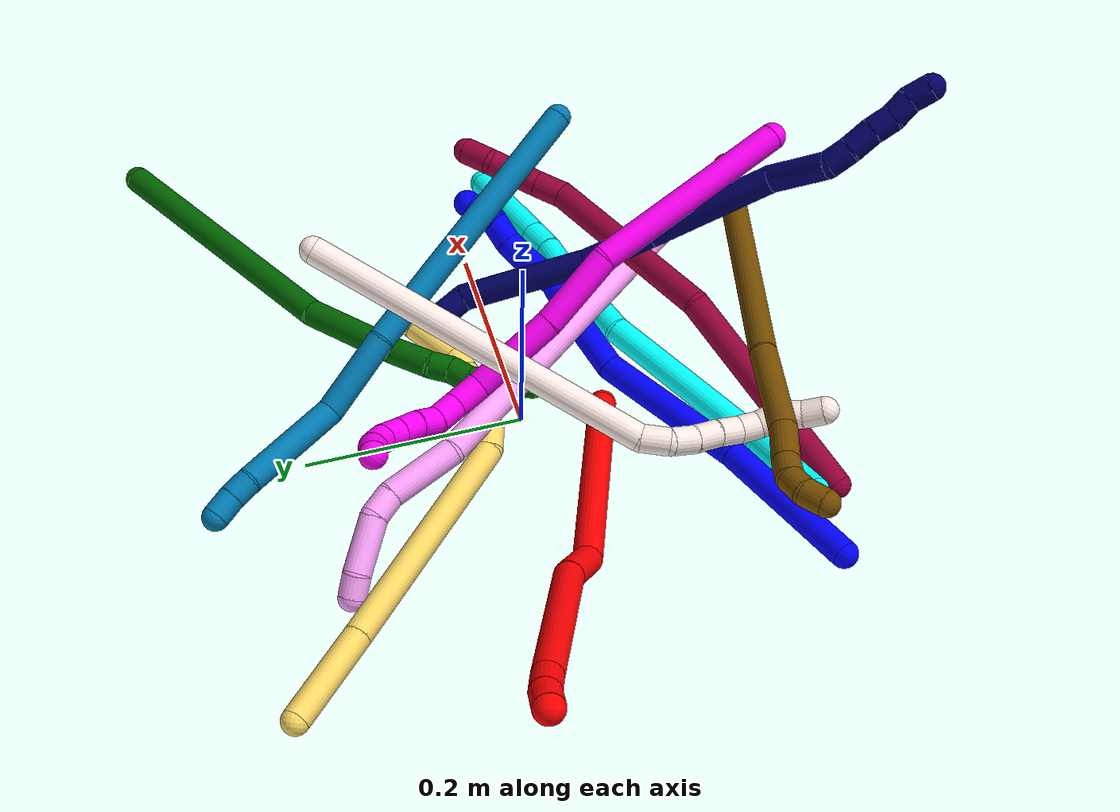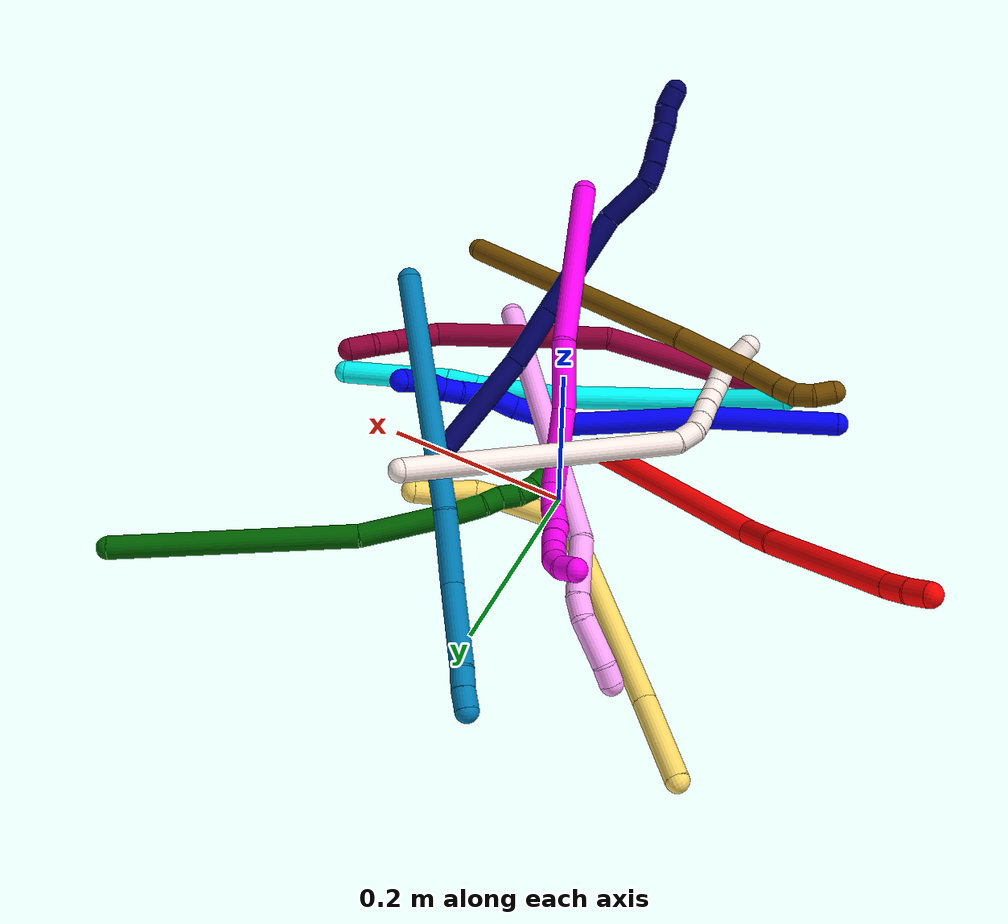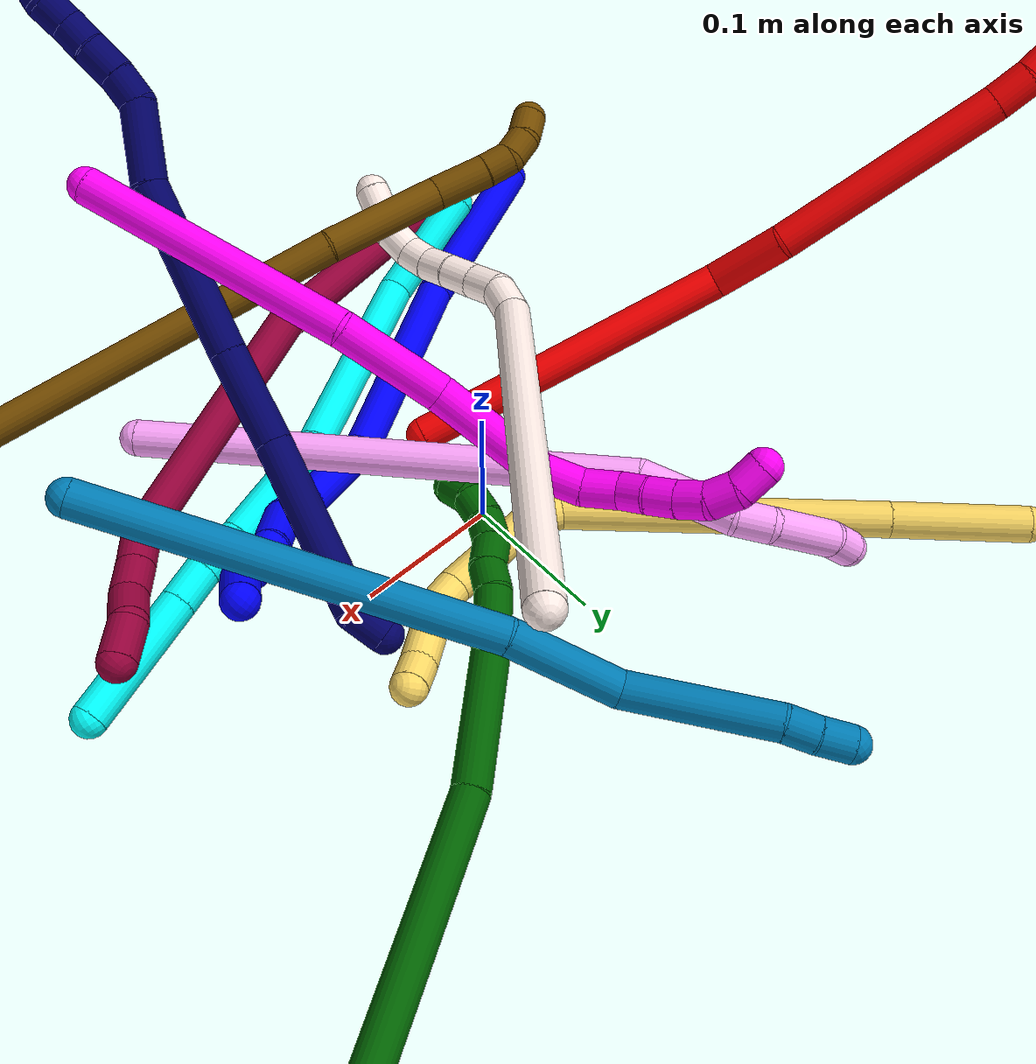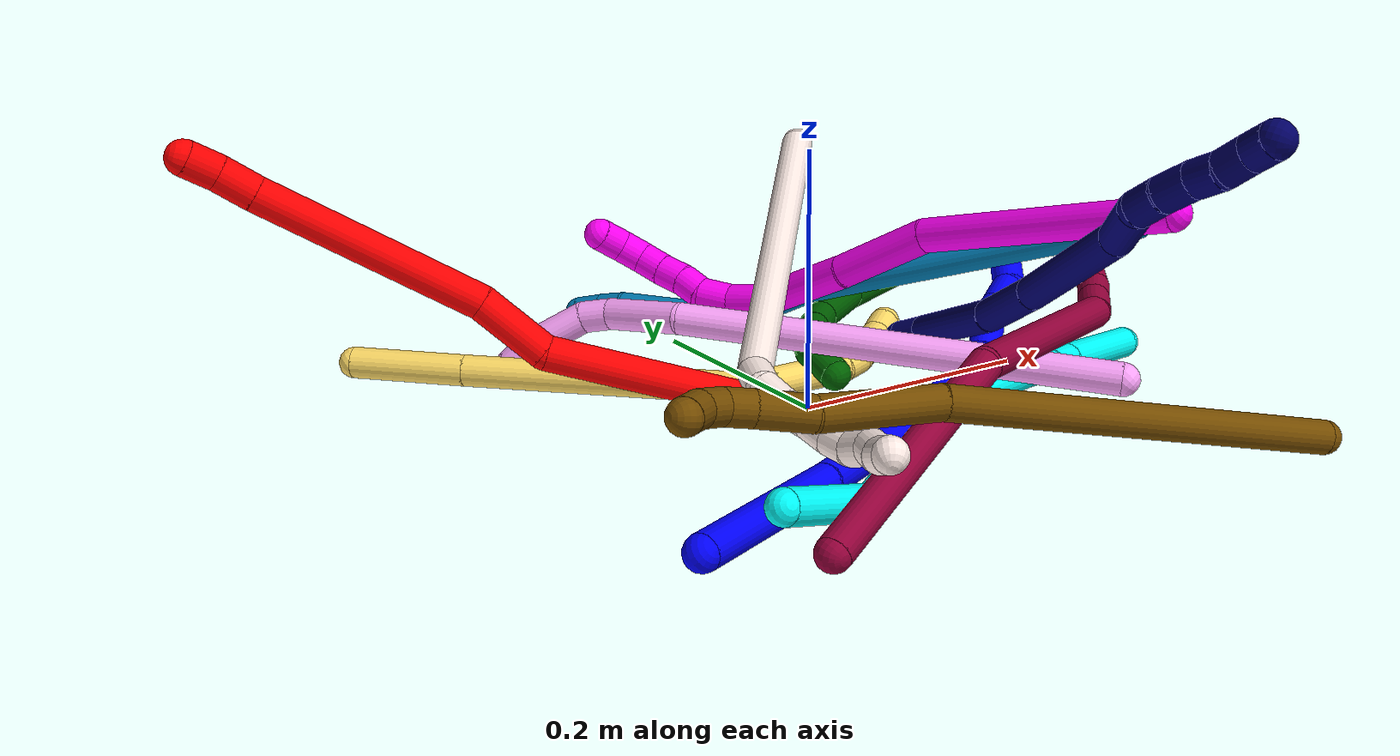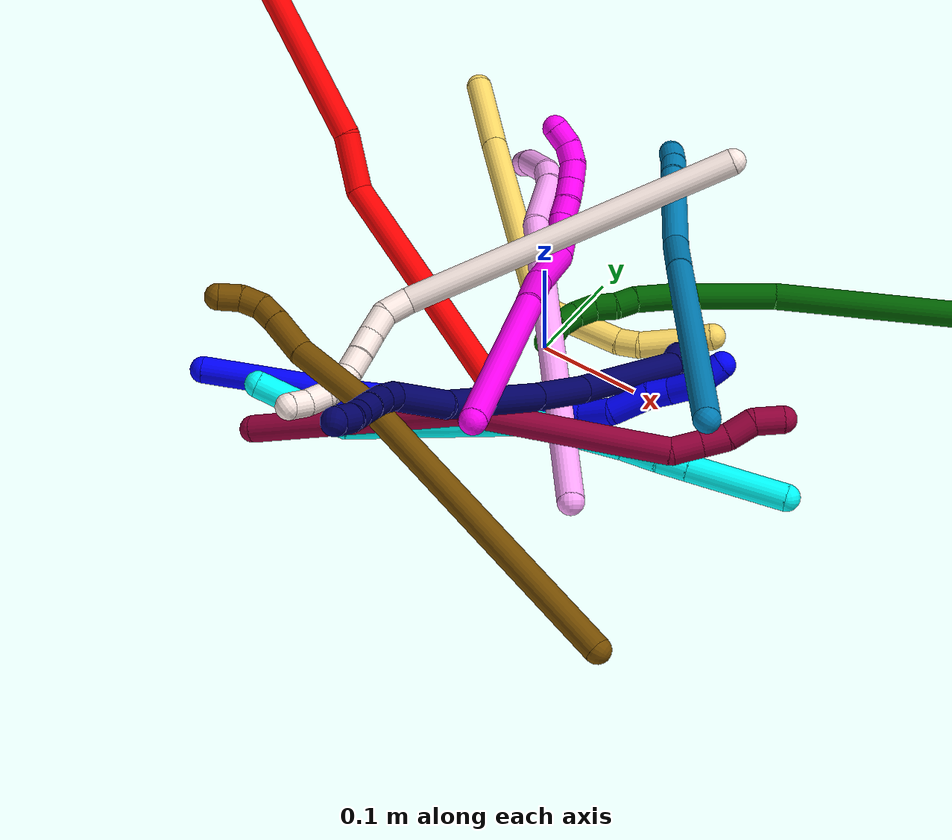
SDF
<sdf version="1.7">
 <world name="default">
  <plugin name="TubeGeneratorPlugin" filename="libtube_generator_plugin.so"/>
  <model name="photoneo_s_sensor">
   <static>1</static>
   <pose>0 0 2 1.57079 1.57079 3.14159</pose>
   <link name="link">
    <inertial><mass>0.1</mass></inertial>
    <sensor name="sensor" type="depth">
     <update_rate>30</update_rate>
     <camera>
      <horizontal_fov>1.22</horizontal_fov>
      <image><width>1920</width><height>1200</height><format>B8G8R8</format></image>
      <clip><near>0.1</near><far>4</far></clip>
      <depth_camera><output>points</output></depth_camera>
     </camera>
     <plugin name="camera_plugin" filename="libgazebo_ros_depth_camera.so">
      <baseline>0.2</baseline>
      <alwaysOn>1</alwaysOn>
      <updateRate>0.0</updateRate>
      <cameraName>camera_ir</cameraName>
      <imageTopicName>/camera/color/image_raw</imageTopicName>
      <cameraInfoTopicName>/camera/color/camera_info</cameraInfoTopicName>
      <depthImageTopicName>/camera/depth/image_raw</depthImageTopicName>
      <depthImageCameraInfoTopicName>/camera/depth/camera_info</depthImageCameraInfoTopicName>
      <pointCloudTopicName>/camera/depth/points</pointCloudTopicName>
      <frameName>fr_optical</frameName>
      <pointCloudCutoff>0.1</pointCloudCutoff>
      <pointCloudCutoffMax>2.0</pointCloudCutoffMax>
      <distortionK1>0</distortionK1>
      <distortionK2>0</distortionK2>
      <distortionK3>0</distortionK3>
      <distortionT1>0</distortionT1>
      <distortionT2>0</distortionT2>
      <CxPrime>0</CxPrime>
      <Cx>0</Cx>
      <Cy>0</Cy>
      <focalLength>0</focalLength>
      <hackBaseline>0</hackBaseline>
     </plugin>
    </sensor>
   </link>
  </model>
  <gravity>0 0 -9.8</gravity>
  <magnetic_field>6e-06 2.3e-05 -4.2e-05</magnetic_field>
  <atmosphere type="adiabatic"/>
  <physics name="default_physics" default="0" type="ode">
   <max_step_size>0.003</max_step_size>
   <real_time_factor>1</real_time_factor>
   <real_time_update_rate>1000</real_time_update_rate>
   <max_contacts>10000</max_contacts>
   <ode>
    <solver>
     <type>quick</type>
     <iters>100</iters>
     <sor>1.3</sor>
     <use_dynamic_moi_rescaling>0</use_dynamic_moi_rescaling>
    </solver>
    <constraints>
     <contact_max_correcting_vel>0</contact_max_correcting_vel>
     <contact_surface_layer>0.001</contact_surface_layer>
     <cfm>0</cfm>
     <erp>0.2</erp>
    </constraints>
   </ode>
  </physics>
  <scene><ambient>0.4 0.4 0.4 1</ambient><background>0.7 0.7 0.7 1</background><shadows>0</shadows></scene>
  <audio><device>default</device></audio>
  <spherical_coordinates>
   <surface_model>EARTH_WGS84</surface_model>
   <latitude_deg>0</latitude_deg>
   <longitude_deg>0</longitude_deg>
   <elevation>0</elevation>
   <heading_deg>0</heading_deg>
  </spherical_coordinates>
  <model name="bin">
   <static>1</static>
   <link name="bottom">
    <collision name="collision-bottom">
     <pose>0 0 -0.01 0 -0 0</pose>
     <geometry><box><size>0.8 0.6 0.02</size></box></geometry>
     <surface>
      <friction><ode><mu>100</mu><mu2>100</mu2></ode></friction>
      <contact><collide_bitmask>65535</collide_bitmask></contact>
     </surface>
    </collision>
   </link>
   <link name="west_wall">
    <collision name="collision-west_wall">
     <pose>-0.41 0 0.1 0 -0 0</pose>
     <geometry><box><size>0.02 0.6 0.2</size></box></geometry>
     <surface>
      <friction><ode><mu>100</mu><mu2>100</mu2></ode></friction>
      <contact><collide_bitmask>65535</collide_bitmask></contact>
     </surface>
    </collision>
   </link>
   <link name="east_wall">
    <collision name="collision-east_wall">
     <pose>0.41 0 0.1 0 -0 0</pose>
     <geometry><box><size>0.02 0.6 0.2</size></box></geometry>
     <surface>
      <friction><ode><mu>100</mu><mu2>100</mu2></ode></friction>
      <contact><collide_bitmask>65535</collide_bitmask></contact>
     </surface>
    </collision>
   </link>
   <link name="south_wall">
    <collision name="collision-south_wall">
     <pose>0 -0.31 0.1 0 -0 0</pose>
     <geometry><box><size>0.8 0.02 0.2</size></box></geometry>
     <surface>
      <friction><ode><mu>100</mu><mu2>100</mu2></ode></friction>
      <contact><collide_bitmask>65535</collide_bitmask></contact>
     </surface>
    </collision>
   </link>
   <link name="north_wall">
    <collision name="collision-north_wall">
     <pose>0 0.31 0.1 0 -0 0</pose>
     <geometry><box><size>0.8 0.02 0.2</size></box></geometry>
     <surface>
      <friction><ode><mu>100</mu><mu2>100</mu2></ode></friction>
      <contact><collide_bitmask>65535</collide_bitmask></contact>
     </surface>
    </collision>
   </link>
  </model>
  <model name="1">
   <static>0</static>
   <link name="1">
    <collision name="collision-cylinder-e_1_1_4">
     <pose>0.066259 0.021722 -0.000694 -1.60273 1.25386 -1.28435</pose>
     <geometry><cylinder><radius>0.0125</radius><length>0.139464</length></cylinder></geometry>
     <surface>
      <friction><ode><mu>1.16</mu><mu2>1.16</mu2><slip1>0</slip1><slip2>0</slip2></ode></friction>
      <contact><ode><kp>1e+06</kp><kd>1</kd><max_vel>0</max_vel><min_depth>0.001</min_depth></ode></contact>
     </surface>
    </collision>
    <visual name="visual-cylinder-e_1_1_4">
     <pose>0.066259 0.021722 -0.000694 -1.60273 1.25386 -1.28435</pose>
     <geometry><cylinder><radius>0.0125</radius><length>0.139464</length></cylinder></geometry>
     <material><ambient>0 0 1 1</ambient></material>
    </visual>
    <collision name="collision-cylinder-e_2_4_5">
     <pose>0.202685 0.069022 -0.00985 -1.8903 1.20418 -1.52079</pose>
     <geometry><cylinder><radius>0.0125</radius><length>0.150324</length></cylinder></geometry>
     <surface>
      <friction><ode><mu>1.16</mu><mu2>1.16</mu2><slip1>0</slip1><slip2>0</slip2></ode></friction>
      <contact><ode><kp>1e+06</kp><kd>1</kd><max_vel>0</max_vel><min_depth>0.001</min_depth></ode></contact>
     </surface>
    </collision>
    <visual name="visual-cylinder-e_2_4_5">
     <pose>0.202685 0.069022 -0.00985 -1.8903 1.20418 -1.52079</pose>
     <geometry><cylinder><radius>0.0125</radius><length>0.150324</length></cylinder></geometry>
     <material><ambient>0 0 1 1</ambient></material>
    </visual>
    <collision name="collision-cylinder-e_3_5_6">
     <pose>0.302407 0.109568 -0.011312 -1.1333 1.06098 -0.714396</pose>
     <geometry><cylinder><radius>0.0125</radius><length>0.06772</length></cylinder></geometry>
     <surface>
      <friction><ode><mu>1.16</mu><mu2>1.16</mu2><slip1>0</slip1><slip2>0</slip2></ode></friction>
      <contact><ode><kp>1e+06</kp><kd>1</kd><max_vel>0</max_vel><min_depth>0.001</min_depth></ode></contact>
     </surface>
    </collision>
    <visual name="visual-cylinder-e_3_5_6">
     <pose>0.302407 0.109568 -0.011312 -1.1333 1.06098 -0.714396</pose>
     <geometry><cylinder><radius>0.0125</radius><length>0.06772</length></cylinder></geometry>
     <material><ambient>0 0 1 1</ambient></material>
    </visual>
    <collision name="collision-cylinder-e_4_6_7">
     <pose>0.343459 0.132893 0.001003 -1.00444 0.859783 -0.493338</pose>
     <geometry><cylinder><radius>0.0125</radius><length>0.030351</length></cylinder></geometry>
     <surface>
      <friction><ode><mu>1.16</mu><mu2>1.16</mu2><slip1>0</slip1><slip2>0</slip2></ode></friction>
      <contact><ode><kp>1e+06</kp><kd>1</kd><max_vel>0</max_vel><min_depth>0.001</min_depth></ode></contact>
     </surface>
    </collision>
    <visual name="visual-cylinder-e_4_6_7">
     <pose>0.343459 0.132893 0.001003 -1.00444 0.859783 -0.493338</pose>
     <geometry><cylinder><radius>0.0125</radius><length>0.030351</length></cylinder></geometry>
     <material><ambient>0 0 1 1</ambient></material>
    </visual>
    <collision name="collision-cylinder-e_5_7_8">
     <pose>0.36691 0.156019 0.006705 -1.54453 0.68023 -0.663874</pose>
     <geometry><cylinder><radius>0.0125</radius><length>0.038005</length></cylinder></geometry>
     <surface>
      <friction><ode><mu>1.16</mu><mu2>1.16</mu2><slip1>0</slip1><slip2>0</slip2></ode></friction>
      <contact><ode><kp>1e+06</kp><kd>1</kd><max_vel>0</max_vel><min_depth>0.001</min_depth></ode></contact>
     </surface>
    </collision>
    <visual name="visual-cylinder-e_5_7_8">
     <pose>0.36691 0.156019 0.006705 -1.54453 0.68023 -0.663874</pose>
     <geometry><cylinder><radius>0.0125</radius><length>0.038005</length></cylinder></geometry>
     <material><ambient>0 0 1 1</ambient></material>
    </visual>
    <collision name="collision-cylinder-e_6_8_9">
     <pose>0.386601 0.177126 0.00799 -1.43028 0.879638 -0.77594</pose>
     <geometry><cylinder><radius>0.0125</radius><length>0.020089</length></cylinder></geometry>
     <surface>
      <friction><ode><mu>1.16</mu><mu2>1.16</mu2><slip1>0</slip1><slip2>0</slip2></ode></friction>
      <contact><ode><kp>1e+06</kp><kd>1</kd><max_vel>0</max_vel><min_depth>0.001</min_depth></ode></contact>
     </surface>
    </collision>
    <visual name="visual-cylinder-e_6_8_9">
     <pose>0.386601 0.177126 0.00799 -1.43028 0.879638 -0.77594</pose>
     <geometry><cylinder><radius>0.0125</radius><length>0.020089</length></cylinder></geometry>
     <material><ambient>0 0 1 1</ambient></material>
    </visual>
    <collision name="collision-cylinder-e_7_9_10">
     <pose>0.402751 0.191257 0.012437 -1.14323 0.776514 -0.51454</pose>
     <geometry><cylinder><radius>0.0125</radius><length>0.024004</length></cylinder></geometry>
     <surface>
      <friction><ode><mu>1.16</mu><mu2>1.16</mu2><slip1>0</slip1><slip2>0</slip2></ode></friction>
      <contact><ode><kp>1e+06</kp><kd>1</kd><max_vel>0</max_vel><min_depth>0.001</min_depth></ode></contact>
     </surface>
    </collision>
    <visual name="visual-cylinder-e_7_9_10">
     <pose>0.402751 0.191257 0.012437 -1.14323 0.776514 -0.51454</pose>
     <geometry><cylinder><radius>0.0125</radius><length>0.024004</length></cylinder></geometry>
     <material><ambient>0 0 1 1</ambient></material>
    </visual>
    <collision name="collision-cylinder-e_8_10_2">
     <pose>0.417875 0.212443 0.014917 -1.65049 0.463263 -0.500206</pose>
     <geometry><cylinder><radius>0.0125</radius><length>0.030043</length></cylinder></geometry>
     <surface>
      <friction><ode><mu>1.16</mu><mu2>1.16</mu2><slip1>0</slip1><slip2>0</slip2></ode></friction>
      <contact><ode><kp>1e+06</kp><kd>1</kd><max_vel>0</max_vel><min_depth>0.001</min_depth></ode></contact>
     </surface>
    </collision>
    <visual name="visual-cylinder-e_8_10_2">
     <pose>0.417875 0.212443 0.014917 -1.65049 0.463263 -0.500206</pose>
     <geometry><cylinder><radius>0.0125</radius><length>0.030043</length></cylinder></geometry>
     <material><ambient>0 0 1 1</ambient></material>
    </visual>
    <collision name="collision-sphere-2">
     <pose>0.424588 0.225839 0.013847 0 -0 0</pose>
     <geometry><sphere><radius>0.0125</radius></sphere></geometry>
     <surface>
      <friction><ode><mu>1.16</mu><mu2>1.16</mu2><slip1>0</slip1><slip2>0</slip2></ode></friction>
      <contact><ode><kp>1e+06</kp><kd>1</kd><max_vel>0</max_vel><min_depth>0.001</min_depth></ode></contact>
     </surface>
    </collision>
    <visual name="visual-sphere-2">
     <pose>0.424588 0.225839 0.013847 0 -0 0</pose>
     <geometry><sphere><radius>0.0125</radius></sphere></geometry>
     <material><ambient>0 0 1 1</ambient></material>
    </visual>
    <collision name="collision-sphere-10">
     <pose>0.411162 0.199048 0.015987 0 -0 0</pose>
     <geometry><sphere><radius>0.0125</radius></sphere></geometry>
     <surface>
      <friction><ode><mu>1.16</mu><mu2>1.16</mu2><slip1>0</slip1><slip2>0</slip2></ode></friction>
      <contact><ode><kp>1e+06</kp><kd>1</kd><max_vel>0</max_vel><min_depth>0.001</min_depth></ode></contact>
     </surface>
    </collision>
    <visual name="visual-sphere-10">
     <pose>0.411162 0.199048 0.015987 0 -0 0</pose>
     <geometry><sphere><radius>0.0125</radius></sphere></geometry>
     <material><ambient>0 0 1 1</ambient></material>
    </visual>
    <collision name="collision-sphere-9">
     <pose>0.39434 0.183466 0.008886 0 -0 0</pose>
     <geometry><sphere><radius>0.0125</radius></sphere></geometry>
     <surface>
      <friction><ode><mu>1.16</mu><mu2>1.16</mu2><slip1>0</slip1><slip2>0</slip2></ode></friction>
      <contact><ode><kp>1e+06</kp><kd>1</kd><max_vel>0</max_vel><min_depth>0.001</min_depth></ode></contact>
     </surface>
    </collision>
    <visual name="visual-sphere-9">
     <pose>0.39434 0.183466 0.008886 0 -0 0</pose>
     <geometry><sphere><radius>0.0125</radius></sphere></geometry>
     <material><ambient>0 0 1 1</ambient></material>
    </visual>
    <collision name="collision-sphere-4">
     <pose>0.132518 0.043443 -0.001388 0 -0 0</pose>
     <geometry><sphere><radius>0.0125</radius></sphere></geometry>
     <surface>
      <friction><ode><mu>1.16</mu><mu2>1.16</mu2><slip1>0</slip1><slip2>0</slip2></ode></friction>
      <contact><ode><kp>1e+06</kp><kd>1</kd><max_vel>0</max_vel><min_depth>0.001</min_depth></ode></contact>
     </surface>
    </collision>
    <visual name="visual-sphere-4">
     <pose>0.132518 0.043443 -0.001388 0 -0 0</pose>
     <geometry><sphere><radius>0.0125</radius></sphere></geometry>
     <material><ambient>0 0 1 1</ambient></material>
    </visual>
    <collision name="collision-sphere-1">
     <geometry><sphere><radius>0.0125</radius></sphere></geometry>
     <surface>
      <friction><ode><mu>1.16</mu><mu2>1.16</mu2><slip1>0</slip1><slip2>0</slip2></ode></friction>
      <contact><ode><kp>1e+06</kp><kd>1</kd><max_vel>0</max_vel><min_depth>0.001</min_depth></ode></contact>
     </surface>
    </collision>
    <visual name="visual-sphere-1">
     <geometry><sphere><radius>0.0125</radius></sphere></geometry>
     <material><ambient>0 0 1 1</ambient></material>
    </visual>
    <collision name="collision-sphere-8">
     <pose>0.378862 0.170787 0.007093 0 -0 0</pose>
     <geometry><sphere><radius>0.0125</radius></sphere></geometry>
     <surface>
      <friction><ode><mu>1.16</mu><mu2>1.16</mu2><slip1>0</slip1><slip2>0</slip2></ode></friction>
      <contact><ode><kp>1e+06</kp><kd>1</kd><max_vel>0</max_vel><min_depth>0.001</min_depth></ode></contact>
     </surface>
    </collision>
    <visual name="visual-sphere-8">
     <pose>0.378862 0.170787 0.007093 0 -0 0</pose>
     <geometry><sphere><radius>0.0125</radius></sphere></geometry>
     <material><ambient>0 0 1 1</ambient></material>
    </visual>
    <collision name="collision-sphere-5">
     <pose>0.272853 0.0946 -0.018313 0 -0 0</pose>
     <geometry><sphere><radius>0.0125</radius></sphere></geometry>
     <surface>
      <friction><ode><mu>1.16</mu><mu2>1.16</mu2><slip1>0</slip1><slip2>0</slip2></ode></friction>
      <contact><ode><kp>1e+06</kp><kd>1</kd><max_vel>0</max_vel><min_depth>0.001</min_depth></ode></contact>
     </surface>
    </collision>
    <visual name="visual-sphere-5">
     <pose>0.272853 0.0946 -0.018313 0 -0 0</pose>
     <geometry><sphere><radius>0.0125</radius></sphere></geometry>
     <material><ambient>0 0 1 1</ambient></material>
    </visual>
    <collision name="collision-sphere-6">
     <pose>0.331961 0.124536 -0.004311 0 -0 0</pose>
     <geometry><sphere><radius>0.0125</radius></sphere></geometry>
     <surface>
      <friction><ode><mu>1.16</mu><mu2>1.16</mu2><slip1>0</slip1><slip2>0</slip2></ode></friction>
      <contact><ode><kp>1e+06</kp><kd>1</kd><max_vel>0</max_vel><min_depth>0.001</min_depth></ode></contact>
     </surface>
    </collision>
    <visual name="visual-sphere-6">
     <pose>0.331961 0.124536 -0.004311 0 -0 0</pose>
     <geometry><sphere><radius>0.0125</radius></sphere></geometry>
     <material><ambient>0 0 1 1</ambient></material>
    </visual>
    <collision name="collision-sphere-7">
     <pose>0.354958 0.141251 0.006317 0 -0 0</pose>
     <geometry><sphere><radius>0.0125</radius></sphere></geometry>
     <surface>
      <friction><ode><mu>1.16</mu><mu2>1.16</mu2><slip1>0</slip1><slip2>0</slip2></ode></friction>
      <contact><ode><kp>1e+06</kp><kd>1</kd><max_vel>0</max_vel><min_depth>0.001</min_depth></ode></contact>
     </surface>
    </collision>
    <visual name="visual-sphere-7">
     <pose>0.354958 0.141251 0.006317 0 -0 0</pose>
     <geometry><sphere><radius>0.0125</radius></sphere></geometry>
     <material><ambient>0 0 1 1</ambient></material>
    </visual>
    <inertial>
     <pose>0.22909 0.090639 -0.002302 0 -0 0</pose>
     <mass>0.5</mass>
     <inertia>
      <ixx>-0.000109</ixx>
      <ixy>0</ixy>
      <ixz>0</ixz>
      <iyy>0.000321</iyy>
      <iyz>0</iyz>
      <izz>-0.000719</izz>
     </inertia>
    </inertial>
   </link>
   <pose>-0.230425 -0.220535 0.022945 0.883502 0.262718 0.196092</pose>
  </model>
  <model name="2">
   <static>0</static>
   <link name="2">
    <collision name="collision-cylinder-e_1_1_4">
     <pose>-0.018141 -0.002774 0.114519 0.024216 -0.157057 -0.001906</pose>
     <geometry><cylinder><radius>0.0125</radius><length>0.23196</length></cylinder></geometry>
     <surface>
      <friction><ode><mu>1.16</mu><mu2>1.16</mu2><slip1>0</slip1><slip2>0</slip2></ode></friction>
      <contact><ode><kp>1e+06</kp><kd>1</kd><max_vel>0</max_vel><min_depth>0.001</min_depth></ode></contact>
     </surface>
    </collision>
    <visual name="visual-cylinder-e_1_1_4">
     <pose>-0.018141 -0.002774 0.114519 0.024216 -0.157057 -0.001906</pose>
     <geometry><cylinder><radius>0.0125</radius><length>0.23196</length></cylinder></geometry>
     <material><ambient>1 0 0 1</ambient></material>
    </visual>
    <collision name="collision-cylinder-e_2_4_5">
     <pose>-0.04564 0.004698 0.252582 -0.410443 -0.349523 0.073471</pose>
     <geometry><cylinder><radius>0.0125</radius><length>0.054657</length></cylinder></geometry>
     <surface>
      <friction><ode><mu>1.16</mu><mu2>1.16</mu2><slip1>0</slip1><slip2>0</slip2></ode></friction>
      <contact><ode><kp>1e+06</kp><kd>1</kd><max_vel>0</max_vel><min_depth>0.001</min_depth></ode></contact>
     </surface>
    </collision>
    <visual name="visual-cylinder-e_2_4_5">
     <pose>-0.04564 0.004698 0.252582 -0.410443 -0.349523 0.073471</pose>
     <geometry><cylinder><radius>0.0125</radius><length>0.054657</length></cylinder></geometry>
     <material><ambient>1 0 0 1</ambient></material>
    </visual>
    <collision name="collision-cylinder-e_3_5_6">
     <pose>-0.069323 0.030337 0.355141 -0.192414 -0.176091 0.017037</pose>
     <geometry><cylinder><radius>0.0125</radius><length>0.16353</length></cylinder></geometry>
     <surface>
      <friction><ode><mu>1.16</mu><mu2>1.16</mu2><slip1>0</slip1><slip2>0</slip2></ode></friction>
      <contact><ode><kp>1e+06</kp><kd>1</kd><max_vel>0</max_vel><min_depth>0.001</min_depth></ode></contact>
     </surface>
    </collision>
    <visual name="visual-cylinder-e_3_5_6">
     <pose>-0.069323 0.030337 0.355141 -0.192414 -0.176091 0.017037</pose>
     <geometry><cylinder><radius>0.0125</radius><length>0.16353</length></cylinder></geometry>
     <material><ambient>1 0 0 1</ambient></material>
    </visual>
    <collision name="collision-cylinder-e_4_6_7">
     <pose>-0.085354 0.049131 0.447128 -0.256303 -0.126675 0.016345</pose>
     <geometry><cylinder><radius>0.0125</radius><length>0.027038</length></cylinder></geometry>
     <surface>
      <friction><ode><mu>1.16</mu><mu2>1.16</mu2><slip1>0</slip1><slip2>0</slip2></ode></friction>
      <contact><ode><kp>1e+06</kp><kd>1</kd><max_vel>0</max_vel><min_depth>0.001</min_depth></ode></contact>
     </surface>
    </collision>
    <visual name="visual-cylinder-e_4_6_7">
     <pose>-0.085354 0.049131 0.447128 -0.256303 -0.126675 0.016345</pose>
     <geometry><cylinder><radius>0.0125</radius><length>0.027038</length></cylinder></geometry>
     <material><ambient>1 0 0 1</ambient></material>
    </visual>
    <collision name="collision-cylinder-e_5_7_2">
     <pose>-0.086562 0.054585 0.47131 -0.181308 0.043835 -0.003985</pose>
     <geometry><cylinder><radius>0.0125</radius><length>0.022815</length></cylinder></geometry>
     <surface>
      <friction><ode><mu>1.16</mu><mu2>1.16</mu2><slip1>0</slip1><slip2>0</slip2></ode></friction>
      <contact><ode><kp>1e+06</kp><kd>1</kd><max_vel>0</max_vel><min_depth>0.001</min_depth></ode></contact>
     </surface>
    </collision>
    <visual name="visual-cylinder-e_5_7_2">
     <pose>-0.086562 0.054585 0.47131 -0.181308 0.043835 -0.003985</pose>
     <geometry><cylinder><radius>0.0125</radius><length>0.022815</length></cylinder></geometry>
     <material><ambient>1 0 0 1</ambient></material>
    </visual>
    <collision name="collision-sphere-2">
     <pose>-0.086062 0.05664 0.48252 0 -0 0</pose>
     <geometry><sphere><radius>0.0125</radius></sphere></geometry>
     <surface>
      <friction><ode><mu>1.16</mu><mu2>1.16</mu2><slip1>0</slip1><slip2>0</slip2></ode></friction>
      <contact><ode><kp>1e+06</kp><kd>1</kd><max_vel>0</max_vel><min_depth>0.001</min_depth></ode></contact>
     </surface>
    </collision>
    <visual name="visual-sphere-2">
     <pose>-0.086062 0.05664 0.48252 0 -0 0</pose>
     <geometry><sphere><radius>0.0125</radius></sphere></geometry>
     <material><ambient>1 0 0 1</ambient></material>
    </visual>
    <collision name="collision-sphere-7">
     <pose>-0.087062 0.05253 0.4601 0 -0 0</pose>
     <geometry><sphere><radius>0.0125</radius></sphere></geometry>
     <surface>
      <friction><ode><mu>1.16</mu><mu2>1.16</mu2><slip1>0</slip1><slip2>0</slip2></ode></friction>
      <contact><ode><kp>1e+06</kp><kd>1</kd><max_vel>0</max_vel><min_depth>0.001</min_depth></ode></contact>
     </surface>
    </collision>
    <visual name="visual-sphere-7">
     <pose>-0.087062 0.05253 0.4601 0 -0 0</pose>
     <geometry><sphere><radius>0.0125</radius></sphere></geometry>
     <material><ambient>1 0 0 1</ambient></material>
    </visual>
    <collision name="collision-sphere-6">
     <pose>-0.083646 0.045731 0.434156 0 -0 0</pose>
     <geometry><sphere><radius>0.0125</radius></sphere></geometry>
     <surface>
      <friction><ode><mu>1.16</mu><mu2>1.16</mu2><slip1>0</slip1><slip2>0</slip2></ode></friction>
      <contact><ode><kp>1e+06</kp><kd>1</kd><max_vel>0</max_vel><min_depth>0.001</min_depth></ode></contact>
     </surface>
    </collision>
    <visual name="visual-sphere-6">
     <pose>-0.083646 0.045731 0.434156 0 -0 0</pose>
     <geometry><sphere><radius>0.0125</radius></sphere></geometry>
     <material><ambient>1 0 0 1</ambient></material>
    </visual>
    <collision name="collision-sphere-5">
     <pose>-0.054999 0.014943 0.276126 0 -0 0</pose>
     <geometry><sphere><radius>0.0125</radius></sphere></geometry>
     <surface>
      <friction><ode><mu>1.16</mu><mu2>1.16</mu2><slip1>0</slip1><slip2>0</slip2></ode></friction>
      <contact><ode><kp>1e+06</kp><kd>1</kd><max_vel>0</max_vel><min_depth>0.001</min_depth></ode></contact>
     </surface>
    </collision>
    <visual name="visual-sphere-5">
     <pose>-0.054999 0.014943 0.276126 0 -0 0</pose>
     <geometry><sphere><radius>0.0125</radius></sphere></geometry>
     <material><ambient>1 0 0 1</ambient></material>
    </visual>
    <collision name="collision-sphere-1">
     <geometry><sphere><radius>0.0125</radius></sphere></geometry>
     <surface>
      <friction><ode><mu>1.16</mu><mu2>1.16</mu2><slip1>0</slip1><slip2>0</slip2></ode></friction>
      <contact><ode><kp>1e+06</kp><kd>1</kd><max_vel>0</max_vel><min_depth>0.001</min_depth></ode></contact>
     </surface>
    </collision>
    <visual name="visual-sphere-1">
     <geometry><sphere><radius>0.0125</radius></sphere></geometry>
     <material><ambient>1 0 0 1</ambient></material>
    </visual>
    <collision name="collision-sphere-4">
     <pose>-0.036281 -0.005547 0.229038 0 -0 0</pose>
     <geometry><sphere><radius>0.0125</radius></sphere></geometry>
     <surface>
      <friction><ode><mu>1.16</mu><mu2>1.16</mu2><slip1>0</slip1><slip2>0</slip2></ode></friction>
      <contact><ode><kp>1e+06</kp><kd>1</kd><max_vel>0</max_vel><min_depth>0.001</min_depth></ode></contact>
     </surface>
    </collision>
    <visual name="visual-sphere-4">
     <pose>-0.036281 -0.005547 0.229038 0 -0 0</pose>
     <geometry><sphere><radius>0.0125</radius></sphere></geometry>
     <material><ambient>1 0 0 1</ambient></material>
    </visual>
    <inertial>
     <pose>-0.044643 0.014296 0.242575 0 -0 0</pose>
     <mass>0.5</mass>
     <inertia>
      <ixx>0.001419</ixx>
      <ixy>0</ixy>
      <ixz>0</ixz>
      <iyy>0.001442</iyy>
      <iyz>0</iyz>
      <izz>0.000221</izz>
     </inertia>
    </inertial>
   </link>
   <pose>-0.010815 -0.073451 0.011546 1.2241 -0.027903 -1.76151</pose>
  </model>
  <model name="3">
   <static>0</static>
   <link name="3">
    <collision name="collision-cylinder-e_1_1_4">
     <pose>0.039881 -0.00477 -0.0186 2.89057 1.12208 2.74528</pose>
     <geometry><cylinder><radius>0.0125</radius><length>0.088526</length></cylinder></geometry>
     <surface>
      <friction><ode><mu>1.16</mu><mu2>1.16</mu2><slip1>0</slip1><slip2>0</slip2></ode></friction>
      <contact><ode><kp>1e+06</kp><kd>1</kd><max_vel>0</max_vel><min_depth>0.001</min_depth></ode></contact>
     </surface>
    </collision>
    <visual name="visual-cylinder-e_1_1_4">
     <pose>0.039881 -0.00477 -0.0186 2.89057 1.12208 2.74528</pose>
     <geometry><cylinder><radius>0.0125</radius><length>0.088526</length></cylinder></geometry>
     <material><ambient>0.003922 1 0.996078 1</ambient></material>
    </visual>
    <collision name="collision-cylinder-e_2_4_5">
     <pose>0.148767 0.019521 -0.076661 -2.50683 0.953255 -2.00838</pose>
     <geometry><cylinder><radius>0.0125</radius><length>0.169273</length></cylinder></geometry>
     <surface>
      <friction><ode><mu>1.16</mu><mu2>1.16</mu2><slip1>0</slip1><slip2>0</slip2></ode></friction>
      <contact><ode><kp>1e+06</kp><kd>1</kd><max_vel>0</max_vel><min_depth>0.001</min_depth></ode></contact>
     </surface>
    </collision>
    <visual name="visual-cylinder-e_2_4_5">
     <pose>0.148767 0.019521 -0.076661 -2.50683 0.953255 -2.00838</pose>
     <geometry><cylinder><radius>0.0125</radius><length>0.169273</length></cylinder></geometry>
     <material><ambient>0.003922 1 0.996078 1</ambient></material>
    </visual>
    <collision name="collision-cylinder-e_3_5_6">
     <pose>0.259223 0.053802 -0.131064 -2.80548 1.20605 -2.65845</pose>
     <geometry><cylinder><radius>0.0125</radius><length>0.088742</length></cylinder></geometry>
     <surface>
      <friction><ode><mu>1.16</mu><mu2>1.16</mu2><slip1>0</slip1><slip2>0</slip2></ode></friction>
      <contact><ode><kp>1e+06</kp><kd>1</kd><max_vel>0</max_vel><min_depth>0.001</min_depth></ode></contact>
     </surface>
    </collision>
    <visual name="visual-cylinder-e_3_5_6">
     <pose>0.259223 0.053802 -0.131064 -2.80548 1.20605 -2.65845</pose>
     <geometry><cylinder><radius>0.0125</radius><length>0.088742</length></cylinder></geometry>
     <material><ambient>0.003922 1 0.996078 1</ambient></material>
    </visual>
    <collision name="collision-cylinder-e_4_6_7">
     <pose>0.317077 0.060271 -0.150291 -2.85812 1.30512 -2.77242</pose>
     <geometry><cylinder><radius>0.0125</radius><length>0.033997</length></cylinder></geometry>
     <surface>
      <friction><ode><mu>1.16</mu><mu2>1.16</mu2><slip1>0</slip1><slip2>0</slip2></ode></friction>
      <contact><ode><kp>1e+06</kp><kd>1</kd><max_vel>0</max_vel><min_depth>0.001</min_depth></ode></contact>
     </surface>
    </collision>
    <visual name="visual-cylinder-e_4_6_7">
     <pose>0.317077 0.060271 -0.150291 -2.85812 1.30512 -2.77242</pose>
     <geometry><cylinder><radius>0.0125</radius><length>0.033997</length></cylinder></geometry>
     <material><ambient>0.003922 1 0.996078 1</ambient></material>
    </visual>
    <collision name="collision-cylinder-e_5_7_8">
     <pose>0.346097 0.062382 -0.15985 -2.97946 1.17018 -2.89753</pose>
     <geometry><cylinder><radius>0.0125</radius><length>0.027407</length></cylinder></geometry>
     <surface>
      <friction><ode><mu>1.16</mu><mu2>1.16</mu2><slip1>0</slip1><slip2>0</slip2></ode></friction>
      <contact><ode><kp>1e+06</kp><kd>1</kd><max_vel>0</max_vel><min_depth>0.001</min_depth></ode></contact>
     </surface>
    </collision>
    <visual name="visual-cylinder-e_5_7_8">
     <pose>0.346097 0.062382 -0.15985 -2.97946 1.17018 -2.89753</pose>
     <geometry><cylinder><radius>0.0125</radius><length>0.027407</length></cylinder></geometry>
     <material><ambient>0.003922 1 0.996078 1</ambient></material>
    </visual>
    <collision name="collision-cylinder-e_6_8_2">
     <pose>0.401213 0.066313 -0.182535 -2.96711 1.17656 -2.88084</pose>
     <geometry><cylinder><radius>0.0125</radius><length>0.092056</length></cylinder></geometry>
     <surface>
      <friction><ode><mu>1.16</mu><mu2>1.16</mu2><slip1>0</slip1><slip2>0</slip2></ode></friction>
      <contact><ode><kp>1e+06</kp><kd>1</kd><max_vel>0</max_vel><min_depth>0.001</min_depth></ode></contact>
     </surface>
    </collision>
    <visual name="visual-cylinder-e_6_8_2">
     <pose>0.401213 0.066313 -0.182535 -2.96711 1.17656 -2.88084</pose>
     <geometry><cylinder><radius>0.0125</radius><length>0.092056</length></cylinder></geometry>
     <material><ambient>0.003922 1 0.996078 1</ambient></material>
    </visual>
    <collision name="collision-sphere-2">
     <pose>0.44371 0.069383 -0.199947 0 -0 0</pose>
     <geometry><sphere><radius>0.0125</radius></sphere></geometry>
     <surface>
      <friction><ode><mu>1.16</mu><mu2>1.16</mu2><slip1>0</slip1><slip2>0</slip2></ode></friction>
      <contact><ode><kp>1e+06</kp><kd>1</kd><max_vel>0</max_vel><min_depth>0.001</min_depth></ode></contact>
     </surface>
    </collision>
    <visual name="visual-sphere-2">
     <pose>0.44371 0.069383 -0.199947 0 -0 0</pose>
     <geometry><sphere><radius>0.0125</radius></sphere></geometry>
     <material><ambient>0.003922 1 0.996078 1</ambient></material>
    </visual>
    <collision name="collision-sphere-4">
     <pose>0.079762 -0.009539 -0.0372 0 -0 0</pose>
     <geometry><sphere><radius>0.0125</radius></sphere></geometry>
     <surface>
      <friction><ode><mu>1.16</mu><mu2>1.16</mu2><slip1>0</slip1><slip2>0</slip2></ode></friction>
      <contact><ode><kp>1e+06</kp><kd>1</kd><max_vel>0</max_vel><min_depth>0.001</min_depth></ode></contact>
     </surface>
    </collision>
    <visual name="visual-sphere-4">
     <pose>0.079762 -0.009539 -0.0372 0 -0 0</pose>
     <geometry><sphere><radius>0.0125</radius></sphere></geometry>
     <material><ambient>0.003922 1 0.996078 1</ambient></material>
    </visual>
    <collision name="collision-sphere-1">
     <geometry><sphere><radius>0.0125</radius></sphere></geometry>
     <surface>
      <friction><ode><mu>1.16</mu><mu2>1.16</mu2><slip1>0</slip1><slip2>0</slip2></ode></friction>
      <contact><ode><kp>1e+06</kp><kd>1</kd><max_vel>0</max_vel><min_depth>0.001</min_depth></ode></contact>
     </surface>
    </collision>
    <visual name="visual-sphere-1">
     <geometry><sphere><radius>0.0125</radius></sphere></geometry>
     <material><ambient>0.003922 1 0.996078 1</ambient></material>
    </visual>
    <collision name="collision-sphere-8">
     <pose>0.358715 0.063244 -0.165124 0 -0 0</pose>
     <geometry><sphere><radius>0.0125</radius></sphere></geometry>
     <surface>
      <friction><ode><mu>1.16</mu><mu2>1.16</mu2><slip1>0</slip1><slip2>0</slip2></ode></friction>
      <contact><ode><kp>1e+06</kp><kd>1</kd><max_vel>0</max_vel><min_depth>0.001</min_depth></ode></contact>
     </surface>
    </collision>
    <visual name="visual-sphere-8">
     <pose>0.358715 0.063244 -0.165124 0 -0 0</pose>
     <geometry><sphere><radius>0.0125</radius></sphere></geometry>
     <material><ambient>0.003922 1 0.996078 1</ambient></material>
    </visual>
    <collision name="collision-sphere-5">
     <pose>0.217771 0.048582 -0.116122 0 -0 0</pose>
     <geometry><sphere><radius>0.0125</radius></sphere></geometry>
     <surface>
      <friction><ode><mu>1.16</mu><mu2>1.16</mu2><slip1>0</slip1><slip2>0</slip2></ode></friction>
      <contact><ode><kp>1e+06</kp><kd>1</kd><max_vel>0</max_vel><min_depth>0.001</min_depth></ode></contact>
     </surface>
    </collision>
    <visual name="visual-sphere-5">
     <pose>0.217771 0.048582 -0.116122 0 -0 0</pose>
     <geometry><sphere><radius>0.0125</radius></sphere></geometry>
     <material><ambient>0.003922 1 0.996078 1</ambient></material>
    </visual>
    <collision name="collision-sphere-6">
     <pose>0.300675 0.059022 -0.146006 0 -0 0</pose>
     <geometry><sphere><radius>0.0125</radius></sphere></geometry>
     <surface>
      <friction><ode><mu>1.16</mu><mu2>1.16</mu2><slip1>0</slip1><slip2>0</slip2></ode></friction>
      <contact><ode><kp>1e+06</kp><kd>1</kd><max_vel>0</max_vel><min_depth>0.001</min_depth></ode></contact>
     </surface>
    </collision>
    <visual name="visual-sphere-6">
     <pose>0.300675 0.059022 -0.146006 0 -0 0</pose>
     <geometry><sphere><radius>0.0125</radius></sphere></geometry>
     <material><ambient>0.003922 1 0.996078 1</ambient></material>
    </visual>
    <collision name="collision-sphere-7">
     <pose>0.333479 0.061519 -0.154576 0 -0 0</pose>
     <geometry><sphere><radius>0.0125</radius></sphere></geometry>
     <surface>
      <friction><ode><mu>1.16</mu><mu2>1.16</mu2><slip1>0</slip1><slip2>0</slip2></ode></friction>
      <contact><ode><kp>1e+06</kp><kd>1</kd><max_vel>0</max_vel><min_depth>0.001</min_depth></ode></contact>
     </surface>
    </collision>
    <visual name="visual-sphere-7">
     <pose>0.333479 0.061519 -0.154576 0 -0 0</pose>
     <geometry><sphere><radius>0.0125</radius></sphere></geometry>
     <material><ambient>0.003922 1 0.996078 1</ambient></material>
    </visual>
    <inertial>
     <pose>0.217831 0.03504 -0.105096 0 -0 0</pose>
     <mass>0.5</mass>
     <inertia>
      <ixx>-0.000361</ixx>
      <ixy>0</ixy>
      <ixz>0</ixz>
      <iyy>0.000298</iyy>
      <iyz>0</iyz>
      <izz>-0.000681</izz>
     </inertia>
    </inertial>
   </link>
   <pose>-0.169124 -0.215888 0.035566 1.05354 -0.03262 -0.075773</pose>
  </model>
  <model name="4">
   <static>0</static>
   <link name="4">
    <collision name="collision-cylinder-e_1_1_4">
     <pose>-0.051968 0.084675 0.137216 -0.55289 -0.311793 0.089123</pose>
     <geometry><cylinder><radius>0.0125</radius><length>0.338815</length></cylinder></geometry>
     <surface>
      <friction><ode><mu>1.16</mu><mu2>1.16</mu2><slip1>0</slip1><slip2>0</slip2></ode></friction>
      <contact><ode><kp>1e+06</kp><kd>1</kd><max_vel>0</max_vel><min_depth>0.001</min_depth></ode></contact>
     </surface>
    </collision>
    <visual name="visual-cylinder-e_1_1_4">
     <pose>-0.051968 0.084675 0.137216 -0.55289 -0.311793 0.089123</pose>
     <geometry><cylinder><radius>0.0125</radius><length>0.338815</length></cylinder></geometry>
     <material><ambient>1 0.65098 0.996078 1</ambient></material>
    </visual>
    <collision name="collision-cylinder-e_2_4_5">
     <pose>-0.107349 0.193216 0.297172 -0.809585 -0.103134 0.04422</pose>
     <geometry><cylinder><radius>0.0125</radius><length>0.066282</length></cylinder></geometry>
     <surface>
      <friction><ode><mu>1.16</mu><mu2>1.16</mu2><slip1>0</slip1><slip2>0</slip2></ode></friction>
      <contact><ode><kp>1e+06</kp><kd>1</kd><max_vel>0</max_vel><min_depth>0.001</min_depth></ode></contact>
     </surface>
    </collision>
    <visual name="visual-cylinder-e_2_4_5">
     <pose>-0.107349 0.193216 0.297172 -0.809585 -0.103134 0.04422</pose>
     <geometry><cylinder><radius>0.0125</radius><length>0.066282</length></cylinder></geometry>
     <material><ambient>1 0.65098 0.996078 1</ambient></material>
    </visual>
    <collision name="collision-cylinder-e_3_5_6">
     <pose>-0.115547 0.224957 0.327732 -0.7888 -0.407164 0.171424</pose>
     <geometry><cylinder><radius>0.0125</radius><length>0.024173</length></cylinder></geometry>
     <surface>
      <friction><ode><mu>1.16</mu><mu2>1.16</mu2><slip1>0</slip1><slip2>0</slip2></ode></friction>
      <contact><ode><kp>1e+06</kp><kd>1</kd><max_vel>0</max_vel><min_depth>0.001</min_depth></ode></contact>
     </surface>
    </collision>
    <visual name="visual-cylinder-e_3_5_6">
     <pose>-0.115547 0.224957 0.327732 -0.7888 -0.407164 0.171424</pose>
     <geometry><cylinder><radius>0.0125</radius><length>0.024173</length></cylinder></geometry>
     <material><ambient>1 0.65098 0.996078 1</ambient></material>
    </visual>
    <collision name="collision-cylinder-e_4_6_7">
     <pose>-0.137091 0.249468 0.344217 -1.09067 -0.729157 0.455067</pose>
     <geometry><cylinder><radius>0.0125</radius><length>0.050304</length></cylinder></geometry>
     <surface>
      <friction><ode><mu>1.16</mu><mu2>1.16</mu2><slip1>0</slip1><slip2>0</slip2></ode></friction>
      <contact><ode><kp>1e+06</kp><kd>1</kd><max_vel>0</max_vel><min_depth>0.001</min_depth></ode></contact>
     </surface>
    </collision>
    <visual name="visual-cylinder-e_4_6_7">
     <pose>-0.137091 0.249468 0.344217 -1.09067 -0.729157 0.455067</pose>
     <geometry><cylinder><radius>0.0125</radius><length>0.050304</length></cylinder></geometry>
     <material><ambient>1 0.65098 0.996078 1</ambient></material>
    </visual>
    <collision name="collision-cylinder-e_5_7_2">
     <pose>-0.160689 0.27364 0.353725 -1.45922 -0.733976 0.662174</pose>
     <geometry><cylinder><radius>0.0125</radius><length>0.020426</length></cylinder></geometry>
     <surface>
      <friction><ode><mu>1.16</mu><mu2>1.16</mu2><slip1>0</slip1><slip2>0</slip2></ode></friction>
      <contact><ode><kp>1e+06</kp><kd>1</kd><max_vel>0</max_vel><min_depth>0.001</min_depth></ode></contact>
     </surface>
    </collision>
    <visual name="visual-cylinder-e_5_7_2">
     <pose>-0.160689 0.27364 0.353725 -1.45922 -0.733976 0.662174</pose>
     <geometry><cylinder><radius>0.0125</radius><length>0.020426</length></cylinder></geometry>
     <material><ambient>1 0.65098 0.996078 1</ambient></material>
    </visual>
    <collision name="collision-sphere-2">
     <pose>-0.16753 0.281176 0.354569 0 -0 0</pose>
     <geometry><sphere><radius>0.0125</radius></sphere></geometry>
     <surface>
      <friction><ode><mu>1.16</mu><mu2>1.16</mu2><slip1>0</slip1><slip2>0</slip2></ode></friction>
      <contact><ode><kp>1e+06</kp><kd>1</kd><max_vel>0</max_vel><min_depth>0.001</min_depth></ode></contact>
     </surface>
    </collision>
    <visual name="visual-sphere-2">
     <pose>-0.16753 0.281176 0.354569 0 -0 0</pose>
     <geometry><sphere><radius>0.0125</radius></sphere></geometry>
     <material><ambient>1 0.65098 0.996078 1</ambient></material>
    </visual>
    <collision name="collision-sphere-7">
     <pose>-0.153848 0.266104 0.35288 0 -0 0</pose>
     <geometry><sphere><radius>0.0125</radius></sphere></geometry>
     <surface>
      <friction><ode><mu>1.16</mu><mu2>1.16</mu2><slip1>0</slip1><slip2>0</slip2></ode></friction>
      <contact><ode><kp>1e+06</kp><kd>1</kd><max_vel>0</max_vel><min_depth>0.001</min_depth></ode></contact>
     </surface>
    </collision>
    <visual name="visual-sphere-7">
     <pose>-0.153848 0.266104 0.35288 0 -0 0</pose>
     <geometry><sphere><radius>0.0125</radius></sphere></geometry>
     <material><ambient>1 0.65098 0.996078 1</ambient></material>
    </visual>
    <collision name="collision-sphere-6">
     <pose>-0.120333 0.232832 0.335553 0 -0 0</pose>
     <geometry><sphere><radius>0.0125</radius></sphere></geometry>
     <surface>
      <friction><ode><mu>1.16</mu><mu2>1.16</mu2><slip1>0</slip1><slip2>0</slip2></ode></friction>
      <contact><ode><kp>1e+06</kp><kd>1</kd><max_vel>0</max_vel><min_depth>0.001</min_depth></ode></contact>
     </surface>
    </collision>
    <visual name="visual-sphere-6">
     <pose>-0.120333 0.232832 0.335553 0 -0 0</pose>
     <geometry><sphere><radius>0.0125</radius></sphere></geometry>
     <material><ambient>1 0.65098 0.996078 1</ambient></material>
    </visual>
    <collision name="collision-sphere-5">
     <pose>-0.110761 0.217083 0.319911 0 -0 0</pose>
     <geometry><sphere><radius>0.0125</radius></sphere></geometry>
     <surface>
      <friction><ode><mu>1.16</mu><mu2>1.16</mu2><slip1>0</slip1><slip2>0</slip2></ode></friction>
      <contact><ode><kp>1e+06</kp><kd>1</kd><max_vel>0</max_vel><min_depth>0.001</min_depth></ode></contact>
     </surface>
    </collision>
    <visual name="visual-sphere-5">
     <pose>-0.110761 0.217083 0.319911 0 -0 0</pose>
     <geometry><sphere><radius>0.0125</radius></sphere></geometry>
     <material><ambient>1 0.65098 0.996078 1</ambient></material>
    </visual>
    <collision name="collision-sphere-1">
     <geometry><sphere><radius>0.0125</radius></sphere></geometry>
     <surface>
      <friction><ode><mu>1.16</mu><mu2>1.16</mu2><slip1>0</slip1><slip2>0</slip2></ode></friction>
      <contact><ode><kp>1e+06</kp><kd>1</kd><max_vel>0</max_vel><min_depth>0.001</min_depth></ode></contact>
     </surface>
    </collision>
    <visual name="visual-sphere-1">
     <geometry><sphere><radius>0.0125</radius></sphere></geometry>
     <material><ambient>1 0.65098 0.996078 1</ambient></material>
    </visual>
    <collision name="collision-sphere-4">
     <pose>-0.103937 0.16935 0.274433 0 -0 0</pose>
     <geometry><sphere><radius>0.0125</radius></sphere></geometry>
     <surface>
      <friction><ode><mu>1.16</mu><mu2>1.16</mu2><slip1>0</slip1><slip2>0</slip2></ode></friction>
      <contact><ode><kp>1e+06</kp><kd>1</kd><max_vel>0</max_vel><min_depth>0.001</min_depth></ode></contact>
     </surface>
    </collision>
    <visual name="visual-sphere-4">
     <pose>-0.103937 0.16935 0.274433 0 -0 0</pose>
     <geometry><sphere><radius>0.0125</radius></sphere></geometry>
     <material><ambient>1 0.65098 0.996078 1</ambient></material>
    </visual>
    <inertial>
     <pose>-0.075389 0.130145 0.197302 0 -0 0</pose>
     <mass>0.5</mass>
     <inertia>
      <ixx>0.003392</ixx>
      <ixy>0</ixy>
      <ixz>0</ixz>
      <iyy>0.003139</iyy>
      <iyz>0</iyz>
      <izz>-0.000618</izz>
     </inertia>
    </inertial>
   </link>
   <pose>0.150867 -0.180179 0.045322 -0.835767 -0.36922 0.335295</pose>
  </model>
  <model name="5">
   <static>0</static>
   <link name="5">
    <collision name="collision-cylinder-e_1_1_4">
     <pose>-0.026913 0.015695 -0.034489 -2.71453 -0.617571 1.94755</pose>
     <geometry><cylinder><radius>0.0125</radius><length>0.092954</length></cylinder></geometry>
     <surface>
      <friction><ode><mu>1.16</mu><mu2>1.16</mu2><slip1>0</slip1><slip2>0</slip2></ode></friction>
      <contact><ode><kp>1e+06</kp><kd>1</kd><max_vel>0</max_vel><min_depth>0.001</min_depth></ode></contact>
     </surface>
    </collision>
    <visual name="visual-cylinder-e_1_1_4">
     <pose>-0.026913 0.015695 -0.034489 -2.71453 -0.617571 1.94755</pose>
     <geometry><cylinder><radius>0.0125</radius><length>0.092954</length></cylinder></geometry>
     <material><ambient>1 0.858824 0.4 1</ambient></material>
    </visual>
    <collision name="collision-cylinder-e_2_4_5">
     <pose>-0.11704 0.069551 -0.152254 -2.71191 -0.60404 1.9196</pose>
     <geometry><cylinder><radius>0.0125</radius><length>0.222597</length></cylinder></geometry>
     <surface>
      <friction><ode><mu>1.16</mu><mu2>1.16</mu2><slip1>0</slip1><slip2>0</slip2></ode></friction>
      <contact><ode><kp>1e+06</kp><kd>1</kd><max_vel>0</max_vel><min_depth>0.001</min_depth></ode></contact>
     </surface>
    </collision>
    <visual name="visual-cylinder-e_2_4_5">
     <pose>-0.11704 0.069551 -0.152254 -2.71191 -0.60404 1.9196</pose>
     <geometry><cylinder><radius>0.0125</radius><length>0.222597</length></cylinder></geometry>
     <material><ambient>1 0.858824 0.4 1</ambient></material>
    </visual>
    <collision name="collision-cylinder-e_3_5_6">
     <pose>-0.182068 0.114026 -0.245145 -2.56046 -0.1564 0.512569</pose>
     <geometry><cylinder><radius>0.0125</radius><length>0.023287</length></cylinder></geometry>
     <surface>
      <friction><ode><mu>1.16</mu><mu2>1.16</mu2><slip1>0</slip1><slip2>0</slip2></ode></friction>
      <contact><ode><kp>1e+06</kp><kd>1</kd><max_vel>0</max_vel><min_depth>0.001</min_depth></ode></contact>
     </surface>
    </collision>
    <visual name="visual-cylinder-e_3_5_6">
     <pose>-0.182068 0.114026 -0.245145 -2.56046 -0.1564 0.512569</pose>
     <geometry><cylinder><radius>0.0125</radius><length>0.023287</length></cylinder></geometry>
     <material><ambient>1 0.858824 0.4 1</ambient></material>
    </visual>
    <collision name="collision-cylinder-e_4_6_7">
     <pose>-0.178191 0.146228 -0.279397 -2.33146 0.157908 -0.364935</pose>
     <geometry><cylinder><radius>0.0125</radius><length>0.072378</length></cylinder></geometry>
     <surface>
      <friction><ode><mu>1.16</mu><mu2>1.16</mu2><slip1>0</slip1><slip2>0</slip2></ode></friction>
      <contact><ode><kp>1e+06</kp><kd>1</kd><max_vel>0</max_vel><min_depth>0.001</min_depth></ode></contact>
     </surface>
    </collision>
    <visual name="visual-cylinder-e_4_6_7">
     <pose>-0.178191 0.146228 -0.279397 -2.33146 0.157908 -0.364935</pose>
     <geometry><cylinder><radius>0.0125</radius><length>0.072378</length></cylinder></geometry>
     <material><ambient>1 0.858824 0.4 1</ambient></material>
    </visual>
    <collision name="collision-cylinder-e_5_7_8">
     <pose>-0.168695 0.178446 -0.31084 -2.39242 0.388663 -0.92828</pose>
     <geometry><cylinder><radius>0.0125</radius><length>0.020085</length></cylinder></geometry>
     <surface>
      <friction><ode><mu>1.16</mu><mu2>1.16</mu2><slip1>0</slip1><slip2>0</slip2></ode></friction>
      <contact><ode><kp>1e+06</kp><kd>1</kd><max_vel>0</max_vel><min_depth>0.001</min_depth></ode></contact>
     </surface>
    </collision>
    <visual name="visual-cylinder-e_5_7_8">
     <pose>-0.168695 0.178446 -0.31084 -2.39242 0.388663 -0.92828</pose>
     <geometry><cylinder><radius>0.0125</radius><length>0.020085</length></cylinder></geometry>
     <material><ambient>1 0.858824 0.4 1</ambient></material>
    </visual>
    <collision name="collision-cylinder-e_6_8_9">
     <pose>-0.149165 0.199288 -0.328674 -2.22061 0.711807 -1.28619</pose>
     <geometry><cylinder><radius>0.0125</radius><length>0.048145</length></cylinder></geometry>
     <surface>
      <friction><ode><mu>1.16</mu><mu2>1.16</mu2><slip1>0</slip1><slip2>0</slip2></ode></friction>
      <contact><ode><kp>1e+06</kp><kd>1</kd><max_vel>0</max_vel><min_depth>0.001</min_depth></ode></contact>
     </surface>
    </collision>
    <visual name="visual-cylinder-e_6_8_9">
     <pose>-0.149165 0.199288 -0.328674 -2.22061 0.711807 -1.28619</pose>
     <geometry><cylinder><radius>0.0125</radius><length>0.048145</length></cylinder></geometry>
     <material><ambient>1 0.858824 0.4 1</ambient></material>
    </visual>
    <collision name="collision-cylinder-e_7_9_2">
     <pose>-0.126529 0.218765 -0.345464 -2.43039 0.737616 -1.61064</pose>
     <geometry><cylinder><radius>0.0125</radius><length>0.020554</length></cylinder></geometry>
     <surface>
      <friction><ode><mu>1.16</mu><mu2>1.16</mu2><slip1>0</slip1><slip2>0</slip2></ode></friction>
      <contact><ode><kp>1e+06</kp><kd>1</kd><max_vel>0</max_vel><min_depth>0.001</min_depth></ode></contact>
     </surface>
    </collision>
    <visual name="visual-cylinder-e_7_9_2">
     <pose>-0.126529 0.218765 -0.345464 -2.43039 0.737616 -1.61064</pose>
     <geometry><cylinder><radius>0.0125</radius><length>0.020554</length></cylinder></geometry>
     <material><ambient>1 0.858824 0.4 1</ambient></material>
    </visual>
    <collision name="collision-sphere-2">
     <pose>-0.119618 0.223729 -0.351225 0 -0 0</pose>
     <geometry><sphere><radius>0.0125</radius></sphere></geometry>
     <surface>
      <friction><ode><mu>1.16</mu><mu2>1.16</mu2><slip1>0</slip1><slip2>0</slip2></ode></friction>
      <contact><ode><kp>1e+06</kp><kd>1</kd><max_vel>0</max_vel><min_depth>0.001</min_depth></ode></contact>
     </surface>
    </collision>
    <visual name="visual-sphere-2">
     <pose>-0.119618 0.223729 -0.351225 0 -0 0</pose>
     <geometry><sphere><radius>0.0125</radius></sphere></geometry>
     <material><ambient>1 0.858824 0.4 1</ambient></material>
    </visual>
    <collision name="collision-sphere-9">
     <pose>-0.133441 0.2138 -0.339702 0 -0 0</pose>
     <geometry><sphere><radius>0.0125</radius></sphere></geometry>
     <surface>
      <friction><ode><mu>1.16</mu><mu2>1.16</mu2><slip1>0</slip1><slip2>0</slip2></ode></friction>
      <contact><ode><kp>1e+06</kp><kd>1</kd><max_vel>0</max_vel><min_depth>0.001</min_depth></ode></contact>
     </surface>
    </collision>
    <visual name="visual-sphere-9">
     <pose>-0.133441 0.2138 -0.339702 0 -0 0</pose>
     <geometry><sphere><radius>0.0125</radius></sphere></geometry>
     <material><ambient>1 0.858824 0.4 1</ambient></material>
    </visual>
    <collision name="collision-sphere-4">
     <pose>-0.053825 0.03139 -0.068977 0 -0 0</pose>
     <geometry><sphere><radius>0.0125</radius></sphere></geometry>
     <surface>
      <friction><ode><mu>1.16</mu><mu2>1.16</mu2><slip1>0</slip1><slip2>0</slip2></ode></friction>
      <contact><ode><kp>1e+06</kp><kd>1</kd><max_vel>0</max_vel><min_depth>0.001</min_depth></ode></contact>
     </surface>
    </collision>
    <visual name="visual-sphere-4">
     <pose>-0.053825 0.03139 -0.068977 0 -0 0</pose>
     <geometry><sphere><radius>0.0125</radius></sphere></geometry>
     <material><ambient>1 0.858824 0.4 1</ambient></material>
    </visual>
    <collision name="collision-sphere-1">
     <geometry><sphere><radius>0.0125</radius></sphere></geometry>
     <surface>
      <friction><ode><mu>1.16</mu><mu2>1.16</mu2><slip1>0</slip1><slip2>0</slip2></ode></friction>
      <contact><ode><kp>1e+06</kp><kd>1</kd><max_vel>0</max_vel><min_depth>0.001</min_depth></ode></contact>
     </surface>
    </collision>
    <visual name="visual-sphere-1">
     <geometry><sphere><radius>0.0125</radius></sphere></geometry>
     <material><ambient>1 0.858824 0.4 1</ambient></material>
    </visual>
    <collision name="collision-sphere-8">
     <pose>-0.164889 0.184775 -0.317646 0 -0 0</pose>
     <geometry><sphere><radius>0.0125</radius></sphere></geometry>
     <surface>
      <friction><ode><mu>1.16</mu><mu2>1.16</mu2><slip1>0</slip1><slip2>0</slip2></ode></friction>
      <contact><ode><kp>1e+06</kp><kd>1</kd><max_vel>0</max_vel><min_depth>0.001</min_depth></ode></contact>
     </surface>
    </collision>
    <visual name="visual-sphere-8">
     <pose>-0.164889 0.184775 -0.317646 0 -0 0</pose>
     <geometry><sphere><radius>0.0125</radius></sphere></geometry>
     <material><ambient>1 0.858824 0.4 1</ambient></material>
    </visual>
    <collision name="collision-sphere-5">
     <pose>-0.180255 0.107712 -0.235532 0 -0 0</pose>
     <geometry><sphere><radius>0.0125</radius></sphere></geometry>
     <surface>
      <friction><ode><mu>1.16</mu><mu2>1.16</mu2><slip1>0</slip1><slip2>0</slip2></ode></friction>
      <contact><ode><kp>1e+06</kp><kd>1</kd><max_vel>0</max_vel><min_depth>0.001</min_depth></ode></contact>
     </surface>
    </collision>
    <visual name="visual-sphere-5">
     <pose>-0.180255 0.107712 -0.235532 0 -0 0</pose>
     <geometry><sphere><radius>0.0125</radius></sphere></geometry>
     <material><ambient>1 0.858824 0.4 1</ambient></material>
    </visual>
    <collision name="collision-sphere-6">
     <pose>-0.183882 0.12034 -0.254758 0 -0 0</pose>
     <geometry><sphere><radius>0.0125</radius></sphere></geometry>
     <surface>
      <friction><ode><mu>1.16</mu><mu2>1.16</mu2><slip1>0</slip1><slip2>0</slip2></ode></friction>
      <contact><ode><kp>1e+06</kp><kd>1</kd><max_vel>0</max_vel><min_depth>0.001</min_depth></ode></contact>
     </surface>
    </collision>
    <visual name="visual-sphere-6">
     <pose>-0.183882 0.12034 -0.254758 0 -0 0</pose>
     <geometry><sphere><radius>0.0125</radius></sphere></geometry>
     <material><ambient>1 0.858824 0.4 1</ambient></material>
    </visual>
    <collision name="collision-sphere-7">
     <pose>-0.1725 0.172117 -0.304035 0 -0 0</pose>
     <geometry><sphere><radius>0.0125</radius></sphere></geometry>
     <surface>
      <friction><ode><mu>1.16</mu><mu2>1.16</mu2><slip1>0</slip1><slip2>0</slip2></ode></friction>
      <contact><ode><kp>1e+06</kp><kd>1</kd><max_vel>0</max_vel><min_depth>0.001</min_depth></ode></contact>
     </surface>
    </collision>
    <visual name="visual-sphere-7">
     <pose>-0.1725 0.172117 -0.304035 0 -0 0</pose>
     <geometry><sphere><radius>0.0125</radius></sphere></geometry>
     <material><ambient>1 0.858824 0.4 1</ambient></material>
    </visual>
    <inertial>
     <pose>-0.117724 0.09571 -0.184392 0 -0 0</pose>
     <mass>0.5</mass>
     <inertia>
      <ixx>0.000495</ixx>
      <ixy>0</ixy>
      <ixz>0</ixz>
      <iyy>0.001283</iyy>
      <iyz>0</iyz>
      <izz>0.00015</izz>
     </inertia>
    </inertial>
   </link>
   <pose>-0.259214 0.261391 0.013244 -2.29048 -0.399683 1.4564</pose>
  </model>
  <model name="6">
   <static>0</static>
   <link name="6">
    <collision name="collision-cylinder-e_1_1_4">
     <pose>-0.007949 0.004768 -0.132329 -3.10557 -0.059958 2.05987</pose>
     <geometry><cylinder><radius>0.0125</radius><length>0.265306</length></cylinder></geometry>
     <surface>
      <friction><ode><mu>1.16</mu><mu2>1.16</mu2><slip1>0</slip1><slip2>0</slip2></ode></friction>
      <contact><ode><kp>1e+06</kp><kd>1</kd><max_vel>0</max_vel><min_depth>0.001</min_depth></ode></contact>
     </surface>
    </collision>
    <visual name="visual-cylinder-e_1_1_4">
     <pose>-0.007949 0.004768 -0.132329 -3.10557 -0.059958 2.05987</pose>
     <geometry><cylinder><radius>0.0125</radius><length>0.265306</length></cylinder></geometry>
     <material><ambient>0 0.392157 0.003922 1</ambient></material>
    </visual>
    <collision name="collision-cylinder-e_2_4_5">
     <pose>-0.027053 0.00757 -0.310499 3.09871 -0.238501 -2.78741</pose>
     <geometry><cylinder><radius>0.0125</radius><length>0.094439</length></cylinder></geometry>
     <surface>
      <friction><ode><mu>1.16</mu><mu2>1.16</mu2><slip1>0</slip1><slip2>0</slip2></ode></friction>
      <contact><ode><kp>1e+06</kp><kd>1</kd><max_vel>0</max_vel><min_depth>0.001</min_depth></ode></contact>
     </surface>
    </collision>
    <visual name="visual-cylinder-e_2_4_5">
     <pose>-0.027053 0.00757 -0.310499 3.09871 -0.238501 -2.78741</pose>
     <geometry><cylinder><radius>0.0125</radius><length>0.094439</length></cylinder></geometry>
     <material><ambient>0 0.392157 0.003922 1</ambient></material>
    </visual>
    <collision name="collision-cylinder-e_3_5_6">
     <pose>-0.044095 0.003461 -0.375305 3.02916 -0.299141 -2.42677</pose>
     <geometry><cylinder><radius>0.0125</radius><length>0.039946</length></cylinder></geometry>
     <surface>
      <friction><ode><mu>1.16</mu><mu2>1.16</mu2><slip1>0</slip1><slip2>0</slip2></ode></friction>
      <contact><ode><kp>1e+06</kp><kd>1</kd><max_vel>0</max_vel><min_depth>0.001</min_depth></ode></contact>
     </surface>
    </collision>
    <visual name="visual-cylinder-e_3_5_6">
     <pose>-0.044095 0.003461 -0.375305 3.02916 -0.299141 -2.42677</pose>
     <geometry><cylinder><radius>0.0125</radius><length>0.039946</length></cylinder></geometry>
     <material><ambient>0 0.392157 0.003922 1</ambient></material>
    </visual>
    <collision name="collision-cylinder-e_4_6_7">
     <pose>-0.053967 -0.001955 -0.40286 2.77741 -0.409219 -1.69005</pose>
     <geometry><cylinder><radius>0.0125</radius><length>0.02004</length></cylinder></geometry>
     <surface>
      <friction><ode><mu>1.16</mu><mu2>1.16</mu2><slip1>0</slip1><slip2>0</slip2></ode></friction>
      <contact><ode><kp>1e+06</kp><kd>1</kd><max_vel>0</max_vel><min_depth>0.001</min_depth></ode></contact>
     </surface>
    </collision>
    <visual name="visual-cylinder-e_4_6_7">
     <pose>-0.053967 -0.001955 -0.40286 2.77741 -0.409219 -1.69005</pose>
     <geometry><cylinder><radius>0.0125</radius><length>0.02004</length></cylinder></geometry>
     <material><ambient>0 0.392157 0.003922 1</ambient></material>
    </visual>
    <collision name="collision-cylinder-e_5_7_8">
     <pose>-0.059712 -0.006402 -0.421255 3.02256 -0.176104 -1.9541</pose>
     <geometry><cylinder><radius>0.0125</radius><length>0.020061</length></cylinder></geometry>
     <surface>
      <friction><ode><mu>1.16</mu><mu2>1.16</mu2><slip1>0</slip1><slip2>0</slip2></ode></friction>
      <contact><ode><kp>1e+06</kp><kd>1</kd><max_vel>0</max_vel><min_depth>0.001</min_depth></ode></contact>
     </surface>
    </collision>
    <visual name="visual-cylinder-e_5_7_8">
     <pose>-0.059712 -0.006402 -0.421255 3.02256 -0.176104 -1.9541</pose>
     <geometry><cylinder><radius>0.0125</radius><length>0.020061</length></cylinder></geometry>
     <material><ambient>0 0.392157 0.003922 1</ambient></material>
    </visual>
    <collision name="collision-cylinder-e_6_8_9">
     <pose>-0.065665 -0.011068 -0.439514 2.74967 -0.430106 -1.66628</pose>
     <geometry><cylinder><radius>0.0125</radius><length>0.020127</length></cylinder></geometry>
     <surface>
      <friction><ode><mu>1.16</mu><mu2>1.16</mu2><slip1>0</slip1><slip2>0</slip2></ode></friction>
      <contact><ode><kp>1e+06</kp><kd>1</kd><max_vel>0</max_vel><min_depth>0.001</min_depth></ode></contact>
     </surface>
    </collision>
    <visual name="visual-cylinder-e_6_8_9">
     <pose>-0.065665 -0.011068 -0.439514 2.74967 -0.430106 -1.66628</pose>
     <geometry><cylinder><radius>0.0125</radius><length>0.020127</length></cylinder></geometry>
     <material><ambient>0 0.392157 0.003922 1</ambient></material>
    </visual>
    <collision name="collision-cylinder-e_7_9_10">
     <pose>-0.075984 -0.018987 -0.454529 2.54825 -0.658432 -1.68178</pose>
     <geometry><cylinder><radius>0.0125</radius><length>0.020011</length></cylinder></geometry>
     <surface>
      <friction><ode><mu>1.16</mu><mu2>1.16</mu2><slip1>0</slip1><slip2>0</slip2></ode></friction>
      <contact><ode><kp>1e+06</kp><kd>1</kd><max_vel>0</max_vel><min_depth>0.001</min_depth></ode></contact>
     </surface>
    </collision>
    <visual name="visual-cylinder-e_7_9_10">
     <pose>-0.075984 -0.018987 -0.454529 2.54825 -0.658432 -1.68178</pose>
     <geometry><cylinder><radius>0.0125</radius><length>0.020011</length></cylinder></geometry>
     <material><ambient>0 0.392157 0.003922 1</ambient></material>
    </visual>
    <collision name="collision-cylinder-e_8_10_2">
     <pose>-0.086731 -0.031048 -0.465671 2.11115 -0.479086 -0.814434</pose>
     <geometry><cylinder><radius>0.0125</radius><length>0.020069</length></cylinder></geometry>
     <surface>
      <friction><ode><mu>1.16</mu><mu2>1.16</mu2><slip1>0</slip1><slip2>0</slip2></ode></friction>
      <contact><ode><kp>1e+06</kp><kd>1</kd><max_vel>0</max_vel><min_depth>0.001</min_depth></ode></contact>
     </surface>
    </collision>
    <visual name="visual-cylinder-e_8_10_2">
     <pose>-0.086731 -0.031048 -0.465671 2.11115 -0.479086 -0.814434</pose>
     <geometry><cylinder><radius>0.0125</radius><length>0.020069</length></cylinder></geometry>
     <material><ambient>0 0.392157 0.003922 1</ambient></material>
    </visual>
    <collision name="collision-sphere-2">
     <pose>-0.091357 -0.038684 -0.470252 0 -0 0</pose>
     <geometry><sphere><radius>0.0125</radius></sphere></geometry>
     <surface>
      <friction><ode><mu>1.16</mu><mu2>1.16</mu2><slip1>0</slip1><slip2>0</slip2></ode></friction>
      <contact><ode><kp>1e+06</kp><kd>1</kd><max_vel>0</max_vel><min_depth>0.001</min_depth></ode></contact>
     </surface>
    </collision>
    <visual name="visual-sphere-2">
     <pose>-0.091357 -0.038684 -0.470252 0 -0 0</pose>
     <geometry><sphere><radius>0.0125</radius></sphere></geometry>
     <material><ambient>0 0.392157 0.003922 1</ambient></material>
    </visual>
    <collision name="collision-sphere-10">
     <pose>-0.082106 -0.023412 -0.46109 0 -0 0</pose>
     <geometry><sphere><radius>0.0125</radius></sphere></geometry>
     <surface>
      <friction><ode><mu>1.16</mu><mu2>1.16</mu2><slip1>0</slip1><slip2>0</slip2></ode></friction>
      <contact><ode><kp>1e+06</kp><kd>1</kd><max_vel>0</max_vel><min_depth>0.001</min_depth></ode></contact>
     </surface>
    </collision>
    <visual name="visual-sphere-10">
     <pose>-0.082106 -0.023412 -0.46109 0 -0 0</pose>
     <geometry><sphere><radius>0.0125</radius></sphere></geometry>
     <material><ambient>0 0.392157 0.003922 1</ambient></material>
    </visual>
    <collision name="collision-sphere-9">
     <pose>-0.069861 -0.014562 -0.447968 0 -0 0</pose>
     <geometry><sphere><radius>0.0125</radius></sphere></geometry>
     <surface>
      <friction><ode><mu>1.16</mu><mu2>1.16</mu2><slip1>0</slip1><slip2>0</slip2></ode></friction>
      <contact><ode><kp>1e+06</kp><kd>1</kd><max_vel>0</max_vel><min_depth>0.001</min_depth></ode></contact>
     </surface>
    </collision>
    <visual name="visual-sphere-9">
     <pose>-0.069861 -0.014562 -0.447968 0 -0 0</pose>
     <geometry><sphere><radius>0.0125</radius></sphere></geometry>
     <material><ambient>0 0.392157 0.003922 1</ambient></material>
    </visual>
    <collision name="collision-sphere-4">
     <pose>-0.015898 0.009536 -0.264658 0 -0 0</pose>
     <geometry><sphere><radius>0.0125</radius></sphere></geometry>
     <surface>
      <friction><ode><mu>1.16</mu><mu2>1.16</mu2><slip1>0</slip1><slip2>0</slip2></ode></friction>
      <contact><ode><kp>1e+06</kp><kd>1</kd><max_vel>0</max_vel><min_depth>0.001</min_depth></ode></contact>
     </surface>
    </collision>
    <visual name="visual-sphere-4">
     <pose>-0.015898 0.009536 -0.264658 0 -0 0</pose>
     <geometry><sphere><radius>0.0125</radius></sphere></geometry>
     <material><ambient>0 0.392157 0.003922 1</ambient></material>
    </visual>
    <collision name="collision-sphere-1">
     <geometry><sphere><radius>0.0125</radius></sphere></geometry>
     <surface>
      <friction><ode><mu>1.16</mu><mu2>1.16</mu2><slip1>0</slip1><slip2>0</slip2></ode></friction>
      <contact><ode><kp>1e+06</kp><kd>1</kd><max_vel>0</max_vel><min_depth>0.001</min_depth></ode></contact>
     </surface>
    </collision>
    <visual name="visual-sphere-1">
     <geometry><sphere><radius>0.0125</radius></sphere></geometry>
     <material><ambient>0 0.392157 0.003922 1</ambient></material>
    </visual>
    <collision name="collision-sphere-8">
     <pose>-0.061469 -0.007574 -0.43106 0 -0 0</pose>
     <geometry><sphere><radius>0.0125</radius></sphere></geometry>
     <surface>
      <friction><ode><mu>1.16</mu><mu2>1.16</mu2><slip1>0</slip1><slip2>0</slip2></ode></friction>
      <contact><ode><kp>1e+06</kp><kd>1</kd><max_vel>0</max_vel><min_depth>0.001</min_depth></ode></contact>
     </surface>
    </collision>
    <visual name="visual-sphere-8">
     <pose>-0.061469 -0.007574 -0.43106 0 -0 0</pose>
     <geometry><sphere><radius>0.0125</radius></sphere></geometry>
     <material><ambient>0 0.392157 0.003922 1</ambient></material>
    </visual>
    <collision name="collision-sphere-5">
     <pose>-0.038209 0.005603 -0.356339 0 -0 0</pose>
     <geometry><sphere><radius>0.0125</radius></sphere></geometry>
     <surface>
      <friction><ode><mu>1.16</mu><mu2>1.16</mu2><slip1>0</slip1><slip2>0</slip2></ode></friction>
      <contact><ode><kp>1e+06</kp><kd>1</kd><max_vel>0</max_vel><min_depth>0.001</min_depth></ode></contact>
     </surface>
    </collision>
    <visual name="visual-sphere-5">
     <pose>-0.038209 0.005603 -0.356339 0 -0 0</pose>
     <geometry><sphere><radius>0.0125</radius></sphere></geometry>
     <material><ambient>0 0.392157 0.003922 1</ambient></material>
    </visual>
    <collision name="collision-sphere-6">
     <pose>-0.04998 0.00132 -0.39427 0 -0 0</pose>
     <geometry><sphere><radius>0.0125</radius></sphere></geometry>
     <surface>
      <friction><ode><mu>1.16</mu><mu2>1.16</mu2><slip1>0</slip1><slip2>0</slip2></ode></friction>
      <contact><ode><kp>1e+06</kp><kd>1</kd><max_vel>0</max_vel><min_depth>0.001</min_depth></ode></contact>
     </surface>
    </collision>
    <visual name="visual-sphere-6">
     <pose>-0.04998 0.00132 -0.39427 0 -0 0</pose>
     <geometry><sphere><radius>0.0125</radius></sphere></geometry>
     <material><ambient>0 0.392157 0.003922 1</ambient></material>
    </visual>
    <collision name="collision-sphere-7">
     <pose>-0.057954 -0.005229 -0.41145 0 -0 0</pose>
     <geometry><sphere><radius>0.0125</radius></sphere></geometry>
     <surface>
      <friction><ode><mu>1.16</mu><mu2>1.16</mu2><slip1>0</slip1><slip2>0</slip2></ode></friction>
      <contact><ode><kp>1e+06</kp><kd>1</kd><max_vel>0</max_vel><min_depth>0.001</min_depth></ode></contact>
     </surface>
    </collision>
    <visual name="visual-sphere-7">
     <pose>-0.057954 -0.005229 -0.41145 0 -0 0</pose>
     <geometry><sphere><radius>0.0125</radius></sphere></geometry>
     <material><ambient>0 0.392157 0.003922 1</ambient></material>
    </visual>
    <inertial>
     <pose>-0.026575 0.001449 -0.246469 0 -0 0</pose>
     <mass>0.5</mass>
     <inertia><ixx>0.000531</ixx><ixy>0</ixy><ixz>0</ixz><iyy>0.002157</iyy><iyz>0</iyz><izz>3e-05</izz></inertia>
    </inertial>
   </link>
   <pose>0.385543 0.288509 0.012323 1.5516 0.643133 2.04289</pose>
  </model>
  <model name="7">
   <static>0</static>
   <link name="7">
    <collision name="collision-cylinder-e_1_1_4">
     <pose>-0.000534 -0.00692 -0.010148 2.54308 -0.04343 -0.140558</pose>
     <geometry><cylinder><radius>0.0125</radius><length>0.024589</length></cylinder></geometry>
     <surface>
      <friction><ode><mu>1.16</mu><mu2>1.16</mu2><slip1>0</slip1><slip2>0</slip2></ode></friction>
      <contact><ode><kp>1e+06</kp><kd>1</kd><max_vel>0</max_vel><min_depth>0.001</min_depth></ode></contact>
     </surface>
    </collision>
    <visual name="visual-cylinder-e_1_1_4">
     <pose>-0.000534 -0.00692 -0.010148 2.54308 -0.04343 -0.140558</pose>
     <geometry><cylinder><radius>0.0125</radius><length>0.024589</length></cylinder></geometry>
     <material><ambient>0.003922 0 0.403922 1</ambient></material>
    </visual>
    <collision name="collision-cylinder-e_2_4_5">
     <pose>-0.032696 -0.049436 -0.058652 2.39352 -0.543674 -1.23498</pose>
     <geometry><cylinder><radius>0.0125</radius><length>0.122288</length></cylinder></geometry>
     <surface>
      <friction><ode><mu>1.16</mu><mu2>1.16</mu2><slip1>0</slip1><slip2>0</slip2></ode></friction>
      <contact><ode><kp>1e+06</kp><kd>1</kd><max_vel>0</max_vel><min_depth>0.001</min_depth></ode></contact>
     </surface>
    </collision>
    <visual name="visual-cylinder-e_2_4_5">
     <pose>-0.032696 -0.049436 -0.058652 2.39352 -0.543674 -1.23498</pose>
     <geometry><cylinder><radius>0.0125</radius><length>0.122288</length></cylinder></geometry>
     <material><ambient>0.003922 0 0.403922 1</ambient></material>
    </visual>
    <collision name="collision-cylinder-e_3_5_6">
     <pose>-0.078484 -0.107855 -0.116606 2.28029 -0.439885 -0.905771</pose>
     <geometry><cylinder><radius>0.0125</radius><length>0.066496</length></cylinder></geometry>
     <surface>
      <friction><ode><mu>1.16</mu><mu2>1.16</mu2><slip1>0</slip1><slip2>0</slip2></ode></friction>
      <contact><ode><kp>1e+06</kp><kd>1</kd><max_vel>0</max_vel><min_depth>0.001</min_depth></ode></contact>
     </surface>
    </collision>
    <visual name="visual-cylinder-e_3_5_6">
     <pose>-0.078484 -0.107855 -0.116606 2.28029 -0.439885 -0.905771</pose>
     <geometry><cylinder><radius>0.0125</radius><length>0.066496</length></cylinder></geometry>
     <material><ambient>0.003922 0 0.403922 1</ambient></material>
    </visual>
    <collision name="collision-cylinder-e_4_6_7">
     <pose>-0.118357 -0.174119 -0.169591 2.22608 -0.438832 -0.850132</pose>
     <geometry><cylinder><radius>0.0125</radius><length>0.121048</length></cylinder></geometry>
     <surface>
      <friction><ode><mu>1.16</mu><mu2>1.16</mu2><slip1>0</slip1><slip2>0</slip2></ode></friction>
      <contact><ode><kp>1e+06</kp><kd>1</kd><max_vel>0</max_vel><min_depth>0.001</min_depth></ode></contact>
     </surface>
    </collision>
    <visual name="visual-cylinder-e_4_6_7">
     <pose>-0.118357 -0.174119 -0.169591 2.22608 -0.438832 -0.850132</pose>
     <geometry><cylinder><radius>0.0125</radius><length>0.121048</length></cylinder></geometry>
     <material><ambient>0.003922 0 0.403922 1</ambient></material>
    </visual>
    <collision name="collision-cylinder-e_5_7_8">
     <pose>-0.161377 -0.237235 -0.2124 2.01735 -0.670613 -1.01059</pose>
     <geometry><cylinder><radius>0.0125</radius><length>0.055688</length></cylinder></geometry>
     <surface>
      <friction><ode><mu>1.16</mu><mu2>1.16</mu2><slip1>0</slip1><slip2>0</slip2></ode></friction>
      <contact><ode><kp>1e+06</kp><kd>1</kd><max_vel>0</max_vel><min_depth>0.001</min_depth></ode></contact>
     </surface>
    </collision>
    <visual name="visual-cylinder-e_5_7_8">
     <pose>-0.161377 -0.237235 -0.2124 2.01735 -0.670613 -1.01059</pose>
     <geometry><cylinder><radius>0.0125</radius><length>0.055688</length></cylinder></geometry>
     <material><ambient>0.003922 0 0.403922 1</ambient></material>
    </visual>
    <collision name="collision-cylinder-e_6_8_9">
     <pose>-0.181222 -0.265265 -0.229223 2.29584 -0.223788 -0.489359</pose>
     <geometry><cylinder><radius>0.0125</radius><length>0.022895</length></cylinder></geometry>
     <surface>
      <friction><ode><mu>1.16</mu><mu2>1.16</mu2><slip1>0</slip1><slip2>0</slip2></ode></friction>
      <contact><ode><kp>1e+06</kp><kd>1</kd><max_vel>0</max_vel><min_depth>0.001</min_depth></ode></contact>
     </surface>
    </collision>
    <visual name="visual-cylinder-e_6_8_9">
     <pose>-0.181222 -0.265265 -0.229223 2.29584 -0.223788 -0.489359</pose>
     <geometry><cylinder><radius>0.0125</radius><length>0.022895</length></cylinder></geometry>
     <material><ambient>0.003922 0 0.403922 1</ambient></material>
    </visual>
    <collision name="collision-cylinder-e_7_9_10">
     <pose>-0.184935 -0.282057 -0.245329 2.37176 -0.096417 -0.237061</pose>
     <geometry><cylinder><radius>0.0125</radius><length>0.024358</length></cylinder></geometry>
     <surface>
      <friction><ode><mu>1.16</mu><mu2>1.16</mu2><slip1>0</slip1><slip2>0</slip2></ode></friction>
      <contact><ode><kp>1e+06</kp><kd>1</kd><max_vel>0</max_vel><min_depth>0.001</min_depth></ode></contact>
     </surface>
    </collision>
    <visual name="visual-cylinder-e_7_9_10">
     <pose>-0.184935 -0.282057 -0.245329 2.37176 -0.096417 -0.237061</pose>
     <geometry><cylinder><radius>0.0125</radius><length>0.024358</length></cylinder></geometry>
     <material><ambient>0.003922 0 0.403922 1</ambient></material>
    </visual>
    <collision name="collision-cylinder-e_8_10_11">
     <pose>-0.188149 -0.296957 -0.26204 2.46248 -0.195862 -0.542546</pose>
     <geometry><cylinder><radius>0.0125</radius><length>0.020982</length></cylinder></geometry>
     <surface>
      <friction><ode><mu>1.16</mu><mu2>1.16</mu2><slip1>0</slip1><slip2>0</slip2></ode></friction>
      <contact><ode><kp>1e+06</kp><kd>1</kd><max_vel>0</max_vel><min_depth>0.001</min_depth></ode></contact>
     </surface>
    </collision>
    <visual name="visual-cylinder-e_8_10_11">
     <pose>-0.188149 -0.296957 -0.26204 2.46248 -0.195862 -0.542546</pose>
     <geometry><cylinder><radius>0.0125</radius><length>0.020982</length></cylinder></geometry>
     <material><ambient>0.003922 0 0.403922 1</ambient></material>
    </visual>
    <collision name="collision-cylinder-e_9_11_12">
     <pose>-0.190048 -0.311028 -0.276867 2.30161 0.013992 0.03133</pose>
     <geometry><cylinder><radius>0.0125</radius><length>0.020436</length></cylinder></geometry>
     <surface>
      <friction><ode><mu>1.16</mu><mu2>1.16</mu2><slip1>0</slip1><slip2>0</slip2></ode></friction>
      <contact><ode><kp>1e+06</kp><kd>1</kd><max_vel>0</max_vel><min_depth>0.001</min_depth></ode></contact>
     </surface>
    </collision>
    <visual name="visual-cylinder-e_9_11_12">
     <pose>-0.190048 -0.311028 -0.276867 2.30161 0.013992 0.03133</pose>
     <geometry><cylinder><radius>0.0125</radius><length>0.020436</length></cylinder></geometry>
     <material><ambient>0.003922 0 0.403922 1</ambient></material>
    </visual>
    <collision name="collision-cylinder-e_10_12_2">
     <pose>-0.193433 -0.326148 -0.290297 2.29247 -0.338993 -0.723809</pose>
     <geometry><cylinder><radius>0.0125</radius><length>0.02122</length></cylinder></geometry>
     <surface>
      <friction><ode><mu>1.16</mu><mu2>1.16</mu2><slip1>0</slip1><slip2>0</slip2></ode></friction>
      <contact><ode><kp>1e+06</kp><kd>1</kd><max_vel>0</max_vel><min_depth>0.001</min_depth></ode></contact>
     </surface>
    </collision>
    <visual name="visual-cylinder-e_10_12_2">
     <pose>-0.193433 -0.326148 -0.290297 2.29247 -0.338993 -0.723809</pose>
     <geometry><cylinder><radius>0.0125</radius><length>0.02122</length></cylinder></geometry>
     <material><ambient>0.003922 0 0.403922 1</ambient></material>
    </visual>
    <collision name="collision-sphere-2">
     <pose>-0.196961 -0.33366 -0.296907 0 -0 0</pose>
     <geometry><sphere><radius>0.0125</radius></sphere></geometry>
     <surface>
      <friction><ode><mu>1.16</mu><mu2>1.16</mu2><slip1>0</slip1><slip2>0</slip2></ode></friction>
      <contact><ode><kp>1e+06</kp><kd>1</kd><max_vel>0</max_vel><min_depth>0.001</min_depth></ode></contact>
     </surface>
    </collision>
    <visual name="visual-sphere-2">
     <pose>-0.196961 -0.33366 -0.296907 0 -0 0</pose>
     <geometry><sphere><radius>0.0125</radius></sphere></geometry>
     <material><ambient>0.003922 0 0.403922 1</ambient></material>
    </visual>
    <collision name="collision-sphere-12">
     <pose>-0.189905 -0.318636 -0.283686 0 -0 0</pose>
     <geometry><sphere><radius>0.0125</radius></sphere></geometry>
     <surface>
      <friction><ode><mu>1.16</mu><mu2>1.16</mu2><slip1>0</slip1><slip2>0</slip2></ode></friction>
      <contact><ode><kp>1e+06</kp><kd>1</kd><max_vel>0</max_vel><min_depth>0.001</min_depth></ode></contact>
     </surface>
    </collision>
    <visual name="visual-sphere-12">
     <pose>-0.189905 -0.318636 -0.283686 0 -0 0</pose>
     <geometry><sphere><radius>0.0125</radius></sphere></geometry>
     <material><ambient>0.003922 0 0.403922 1</ambient></material>
    </visual>
    <collision name="collision-sphere-11">
     <pose>-0.190191 -0.30342 -0.270047 0 -0 0</pose>
     <geometry><sphere><radius>0.0125</radius></sphere></geometry>
     <surface>
      <friction><ode><mu>1.16</mu><mu2>1.16</mu2><slip1>0</slip1><slip2>0</slip2></ode></friction>
      <contact><ode><kp>1e+06</kp><kd>1</kd><max_vel>0</max_vel><min_depth>0.001</min_depth></ode></contact>
     </surface>
    </collision>
    <visual name="visual-sphere-11">
     <pose>-0.190191 -0.30342 -0.270047 0 -0 0</pose>
     <geometry><sphere><radius>0.0125</radius></sphere></geometry>
     <material><ambient>0.003922 0 0.403922 1</ambient></material>
    </visual>
    <collision name="collision-sphere-10">
     <pose>-0.186107 -0.290494 -0.254033 0 -0 0</pose>
     <geometry><sphere><radius>0.0125</radius></sphere></geometry>
     <surface>
      <friction><ode><mu>1.16</mu><mu2>1.16</mu2><slip1>0</slip1><slip2>0</slip2></ode></friction>
      <contact><ode><kp>1e+06</kp><kd>1</kd><max_vel>0</max_vel><min_depth>0.001</min_depth></ode></contact>
     </surface>
    </collision>
    <visual name="visual-sphere-10">
     <pose>-0.186107 -0.290494 -0.254033 0 -0 0</pose>
     <geometry><sphere><radius>0.0125</radius></sphere></geometry>
     <material><ambient>0.003922 0 0.403922 1</ambient></material>
    </visual>
    <collision name="collision-sphere-9">
     <pose>-0.183762 -0.273619 -0.236625 0 -0 0</pose>
     <geometry><sphere><radius>0.0125</radius></sphere></geometry>
     <surface>
      <friction><ode><mu>1.16</mu><mu2>1.16</mu2><slip1>0</slip1><slip2>0</slip2></ode></friction>
      <contact><ode><kp>1e+06</kp><kd>1</kd><max_vel>0</max_vel><min_depth>0.001</min_depth></ode></contact>
     </surface>
    </collision>
    <visual name="visual-sphere-9">
     <pose>-0.183762 -0.273619 -0.236625 0 -0 0</pose>
     <geometry><sphere><radius>0.0125</radius></sphere></geometry>
     <material><ambient>0.003922 0 0.403922 1</ambient></material>
    </visual>
    <collision name="collision-sphere-4">
     <pose>-0.001068 -0.01384 -0.020295 0 -0 0</pose>
     <geometry><sphere><radius>0.0125</radius></sphere></geometry>
     <surface>
      <friction><ode><mu>1.16</mu><mu2>1.16</mu2><slip1>0</slip1><slip2>0</slip2></ode></friction>
      <contact><ode><kp>1e+06</kp><kd>1</kd><max_vel>0</max_vel><min_depth>0.001</min_depth></ode></contact>
     </surface>
    </collision>
    <visual name="visual-sphere-4">
     <pose>-0.001068 -0.01384 -0.020295 0 -0 0</pose>
     <geometry><sphere><radius>0.0125</radius></sphere></geometry>
     <material><ambient>0.003922 0 0.403922 1</ambient></material>
    </visual>
    <collision name="collision-sphere-1">
     <geometry><sphere><radius>0.0125</radius></sphere></geometry>
     <surface>
      <friction><ode><mu>1.16</mu><mu2>1.16</mu2><slip1>0</slip1><slip2>0</slip2></ode></friction>
      <contact><ode><kp>1e+06</kp><kd>1</kd><max_vel>0</max_vel><min_depth>0.001</min_depth></ode></contact>
     </surface>
    </collision>
    <visual name="visual-sphere-1">
     <geometry><sphere><radius>0.0125</radius></sphere></geometry>
     <material><ambient>0.003922 0 0.403922 1</ambient></material>
    </visual>
    <collision name="collision-sphere-8">
     <pose>-0.178682 -0.256911 -0.22182 0 -0 0</pose>
     <geometry><sphere><radius>0.0125</radius></sphere></geometry>
     <surface>
      <friction><ode><mu>1.16</mu><mu2>1.16</mu2><slip1>0</slip1><slip2>0</slip2></ode></friction>
      <contact><ode><kp>1e+06</kp><kd>1</kd><max_vel>0</max_vel><min_depth>0.001</min_depth></ode></contact>
     </surface>
    </collision>
    <visual name="visual-sphere-8">
     <pose>-0.178682 -0.256911 -0.22182 0 -0 0</pose>
     <geometry><sphere><radius>0.0125</radius></sphere></geometry>
     <material><ambient>0.003922 0 0.403922 1</ambient></material>
    </visual>
    <collision name="collision-sphere-5">
     <pose>-0.064325 -0.085031 -0.097008 0 -0 0</pose>
     <geometry><sphere><radius>0.0125</radius></sphere></geometry>
     <surface>
      <friction><ode><mu>1.16</mu><mu2>1.16</mu2><slip1>0</slip1><slip2>0</slip2></ode></friction>
      <contact><ode><kp>1e+06</kp><kd>1</kd><max_vel>0</max_vel><min_depth>0.001</min_depth></ode></contact>
     </surface>
    </collision>
    <visual name="visual-sphere-5">
     <pose>-0.064325 -0.085031 -0.097008 0 -0 0</pose>
     <geometry><sphere><radius>0.0125</radius></sphere></geometry>
     <material><ambient>0.003922 0 0.403922 1</ambient></material>
    </visual>
    <collision name="collision-sphere-6">
     <pose>-0.092642 -0.130678 -0.136203 0 -0 0</pose>
     <geometry><sphere><radius>0.0125</radius></sphere></geometry>
     <surface>
      <friction><ode><mu>1.16</mu><mu2>1.16</mu2><slip1>0</slip1><slip2>0</slip2></ode></friction>
      <contact><ode><kp>1e+06</kp><kd>1</kd><max_vel>0</max_vel><min_depth>0.001</min_depth></ode></contact>
     </surface>
    </collision>
    <visual name="visual-sphere-6">
     <pose>-0.092642 -0.130678 -0.136203 0 -0 0</pose>
     <geometry><sphere><radius>0.0125</radius></sphere></geometry>
     <material><ambient>0.003922 0 0.403922 1</ambient></material>
    </visual>
    <collision name="collision-sphere-7">
     <pose>-0.144073 -0.21756 -0.202979 0 -0 0</pose>
     <geometry><sphere><radius>0.0125</radius></sphere></geometry>
     <surface>
      <friction><ode><mu>1.16</mu><mu2>1.16</mu2><slip1>0</slip1><slip2>0</slip2></ode></friction>
      <contact><ode><kp>1e+06</kp><kd>1</kd><max_vel>0</max_vel><min_depth>0.001</min_depth></ode></contact>
     </surface>
    </collision>
    <visual name="visual-sphere-7">
     <pose>-0.144073 -0.21756 -0.202979 0 -0 0</pose>
     <geometry><sphere><radius>0.0125</radius></sphere></geometry>
     <material><ambient>0.003922 0 0.403922 1</ambient></material>
    </visual>
    <inertial>
     <pose>-0.106268 -0.160253 -0.152145 0 -0 0</pose>
     <mass>0.5</mass>
     <inertia>
      <ixx>-0.000113</ixx>
      <ixy>0</ixy>
      <ixz>0</ixz>
      <iyy>-0.000306</iyy>
      <iyz>0</iyz>
      <izz>0.000385</izz>
     </inertia>
    </inertial>
   </link>
   <pose>0.121063 0.041612 0.024788 -1.36496 -0.127894 0.414051</pose>
  </model>
  <model name="8">
   <static>0</static>
   <link name="8">
    <collision name="collision-cylinder-e_1_1_4">
     <pose>0.058775 0.077717 -0.034126 -1.98455 0.605646 -0.89246</pose>
     <geometry><cylinder><radius>0.0125</radius><length>0.206485</length></cylinder></geometry>
     <surface>
      <friction><ode><mu>1.16</mu><mu2>1.16</mu2><slip1>0</slip1><slip2>0</slip2></ode></friction>
      <contact><ode><kp>1e+06</kp><kd>1</kd><max_vel>0</max_vel><min_depth>0.001</min_depth></ode></contact>
     </surface>
    </collision>
    <visual name="visual-cylinder-e_1_1_4">
     <pose>0.058775 0.077717 -0.034126 -1.98455 0.605646 -0.89246</pose>
     <geometry><cylinder><radius>0.0125</radius><length>0.206485</length></cylinder></geometry>
     <material><ambient>0.584314 0 0.227451 1</ambient></material>
    </visual>
    <collision name="collision-cylinder-e_2_4_5">
     <pose>0.194729 0.199243 -0.10027 -2.20195 0.958009 -1.59339</pose>
     <geometry><cylinder><radius>0.0125</radius><length>0.188689</length></cylinder></geometry>
     <surface>
      <friction><ode><mu>1.16</mu><mu2>1.16</mu2><slip1>0</slip1><slip2>0</slip2></ode></friction>
      <contact><ode><kp>1e+06</kp><kd>1</kd><max_vel>0</max_vel><min_depth>0.001</min_depth></ode></contact>
     </surface>
    </collision>
    <visual name="visual-cylinder-e_2_4_5">
     <pose>0.194729 0.199243 -0.10027 -2.20195 0.958009 -1.59339</pose>
     <geometry><cylinder><radius>0.0125</radius><length>0.188689</length></cylinder></geometry>
     <material><ambient>0.584314 0 0.227451 1</ambient></material>
    </visual>
    <collision name="collision-cylinder-e_3_5_6">
     <pose>0.279301 0.249259 -0.142052 -2.57527 0.568611 -1.57506</pose>
     <geometry><cylinder><radius>0.0125</radius><length>0.027461</length></cylinder></geometry>
     <surface>
      <friction><ode><mu>1.16</mu><mu2>1.16</mu2><slip1>0</slip1><slip2>0</slip2></ode></friction>
      <contact><ode><kp>1e+06</kp><kd>1</kd><max_vel>0</max_vel><min_depth>0.001</min_depth></ode></contact>
     </surface>
    </collision>
    <visual name="visual-cylinder-e_3_5_6">
     <pose>0.279301 0.249259 -0.142052 -2.57527 0.568611 -1.57506</pose>
     <geometry><cylinder><radius>0.0125</radius><length>0.027461</length></cylinder></geometry>
     <material><ambient>0.584314 0 0.227451 1</ambient></material>
    </visual>
    <collision name="collision-cylinder-e_4_6_7">
     <pose>0.293212 0.261345 -0.160277 -2.53443 0.564099 -1.49292</pose>
     <geometry><cylinder><radius>0.0125</radius><length>0.024384</length></cylinder></geometry>
     <surface>
      <friction><ode><mu>1.16</mu><mu2>1.16</mu2><slip1>0</slip1><slip2>0</slip2></ode></friction>
      <contact><ode><kp>1e+06</kp><kd>1</kd><max_vel>0</max_vel><min_depth>0.001</min_depth></ode></contact>
     </surface>
    </collision>
    <visual name="visual-cylinder-e_4_6_7">
     <pose>0.293212 0.261345 -0.160277 -2.53443 0.564099 -1.49292</pose>
     <geometry><cylinder><radius>0.0125</radius><length>0.024384</length></cylinder></geometry>
     <material><ambient>0.584314 0 0.227451 1</ambient></material>
    </visual>
    <collision name="collision-cylinder-e_5_7_8">
     <pose>0.30312 0.274362 -0.179062 -2.53657 0.263715 -0.803681</pose>
     <geometry><cylinder><radius>0.0125</radius><length>0.026</length></cylinder></geometry>
     <surface>
      <friction><ode><mu>1.16</mu><mu2>1.16</mu2><slip1>0</slip1><slip2>0</slip2></ode></friction>
      <contact><ode><kp>1e+06</kp><kd>1</kd><max_vel>0</max_vel><min_depth>0.001</min_depth></ode></contact>
     </surface>
    </collision>
    <visual name="visual-cylinder-e_5_7_8">
     <pose>0.30312 0.274362 -0.179062 -2.53657 0.263715 -0.803681</pose>
     <geometry><cylinder><radius>0.0125</radius><length>0.026</length></cylinder></geometry>
     <material><ambient>0.584314 0 0.227451 1</ambient></material>
    </visual>
    <collision name="collision-cylinder-e_6_8_2">
     <pose>0.315644 0.286907 -0.197709 -2.56558 0.743975 -1.84273</pose>
     <geometry><cylinder><radius>0.0125</radius><length>0.026981</length></cylinder></geometry>
     <surface>
      <friction><ode><mu>1.16</mu><mu2>1.16</mu2><slip1>0</slip1><slip2>0</slip2></ode></friction>
      <contact><ode><kp>1e+06</kp><kd>1</kd><max_vel>0</max_vel><min_depth>0.001</min_depth></ode></contact>
     </surface>
    </collision>
    <visual name="visual-cylinder-e_6_8_2">
     <pose>0.315644 0.286907 -0.197709 -2.56558 0.743975 -1.84273</pose>
     <geometry><cylinder><radius>0.0125</radius><length>0.026981</length></cylinder></geometry>
     <material><ambient>0.584314 0 0.227451 1</ambient></material>
    </visual>
    <collision name="collision-sphere-2">
     <pose>0.32478 0.292314 -0.206033 0 -0 0</pose>
     <geometry><sphere><radius>0.0125</radius></sphere></geometry>
     <surface>
      <friction><ode><mu>1.16</mu><mu2>1.16</mu2><slip1>0</slip1><slip2>0</slip2></ode></friction>
      <contact><ode><kp>1e+06</kp><kd>1</kd><max_vel>0</max_vel><min_depth>0.001</min_depth></ode></contact>
     </surface>
    </collision>
    <visual name="visual-sphere-2">
     <pose>0.32478 0.292314 -0.206033 0 -0 0</pose>
     <geometry><sphere><radius>0.0125</radius></sphere></geometry>
     <material><ambient>0.584314 0 0.227451 1</ambient></material>
    </visual>
    <collision name="collision-sphere-4">
     <pose>0.117551 0.155434 -0.068251 0 -0 0</pose>
     <geometry><sphere><radius>0.0125</radius></sphere></geometry>
     <surface>
      <friction><ode><mu>1.16</mu><mu2>1.16</mu2><slip1>0</slip1><slip2>0</slip2></ode></friction>
      <contact><ode><kp>1e+06</kp><kd>1</kd><max_vel>0</max_vel><min_depth>0.001</min_depth></ode></contact>
     </surface>
    </collision>
    <visual name="visual-sphere-4">
     <pose>0.117551 0.155434 -0.068251 0 -0 0</pose>
     <geometry><sphere><radius>0.0125</radius></sphere></geometry>
     <material><ambient>0.584314 0 0.227451 1</ambient></material>
    </visual>
    <collision name="collision-sphere-1">
     <geometry><sphere><radius>0.0125</radius></sphere></geometry>
     <surface>
      <friction><ode><mu>1.16</mu><mu2>1.16</mu2><slip1>0</slip1><slip2>0</slip2></ode></friction>
      <contact><ode><kp>1e+06</kp><kd>1</kd><max_vel>0</max_vel><min_depth>0.001</min_depth></ode></contact>
     </surface>
    </collision>
    <visual name="visual-sphere-1">
     <geometry><sphere><radius>0.0125</radius></sphere></geometry>
     <material><ambient>0.584314 0 0.227451 1</ambient></material>
    </visual>
    <collision name="collision-sphere-8">
     <pose>0.306508 0.2815 -0.189384 0 -0 0</pose>
     <geometry><sphere><radius>0.0125</radius></sphere></geometry>
     <surface>
      <friction><ode><mu>1.16</mu><mu2>1.16</mu2><slip1>0</slip1><slip2>0</slip2></ode></friction>
      <contact><ode><kp>1e+06</kp><kd>1</kd><max_vel>0</max_vel><min_depth>0.001</min_depth></ode></contact>
     </surface>
    </collision>
    <visual name="visual-sphere-8">
     <pose>0.306508 0.2815 -0.189384 0 -0 0</pose>
     <geometry><sphere><radius>0.0125</radius></sphere></geometry>
     <material><ambient>0.584314 0 0.227451 1</ambient></material>
    </visual>
    <collision name="collision-sphere-5">
     <pose>0.271907 0.243051 -0.132288 0 -0 0</pose>
     <geometry><sphere><radius>0.0125</radius></sphere></geometry>
     <surface>
      <friction><ode><mu>1.16</mu><mu2>1.16</mu2><slip1>0</slip1><slip2>0</slip2></ode></friction>
      <contact><ode><kp>1e+06</kp><kd>1</kd><max_vel>0</max_vel><min_depth>0.001</min_depth></ode></contact>
     </surface>
    </collision>
    <visual name="visual-sphere-5">
     <pose>0.271907 0.243051 -0.132288 0 -0 0</pose>
     <geometry><sphere><radius>0.0125</radius></sphere></geometry>
     <material><ambient>0.584314 0 0.227451 1</ambient></material>
    </visual>
    <collision name="collision-sphere-6">
     <pose>0.286694 0.255467 -0.151816 0 -0 0</pose>
     <geometry><sphere><radius>0.0125</radius></sphere></geometry>
     <surface>
      <friction><ode><mu>1.16</mu><mu2>1.16</mu2><slip1>0</slip1><slip2>0</slip2></ode></friction>
      <contact><ode><kp>1e+06</kp><kd>1</kd><max_vel>0</max_vel><min_depth>0.001</min_depth></ode></contact>
     </surface>
    </collision>
    <visual name="visual-sphere-6">
     <pose>0.286694 0.255467 -0.151816 0 -0 0</pose>
     <geometry><sphere><radius>0.0125</radius></sphere></geometry>
     <material><ambient>0.584314 0 0.227451 1</ambient></material>
    </visual>
    <collision name="collision-sphere-7">
     <pose>0.299731 0.267223 -0.168739 0 -0 0</pose>
     <geometry><sphere><radius>0.0125</radius></sphere></geometry>
     <surface>
      <friction><ode><mu>1.16</mu><mu2>1.16</mu2><slip1>0</slip1><slip2>0</slip2></ode></friction>
      <contact><ode><kp>1e+06</kp><kd>1</kd><max_vel>0</max_vel><min_depth>0.001</min_depth></ode></contact>
     </surface>
    </collision>
    <visual name="visual-sphere-7">
     <pose>0.299731 0.267223 -0.168739 0 -0 0</pose>
     <geometry><sphere><radius>0.0125</radius></sphere></geometry>
     <material><ambient>0.584314 0 0.227451 1</ambient></material>
    </visual>
    <inertial>
     <pose>0.160193 0.163469 -0.087531 0 -0 0</pose>
     <mass>0.5</mass>
     <inertia>
      <ixx>-0.000407</ixx>
      <ixy>0</ixy>
      <ixz>0</ixz>
      <iyy>-0.000288</iyy>
      <iyz>0</iyz>
      <izz>-0.001734</izz>
     </inertia>
    </inertial>
   </link>
   <pose>-0.153156 -0.245557 0.011963 1.6271 0.59494 0.082886</pose>
  </model>
  <model name="9">
   <static>0</static>
   <link name="9">
    <collision name="collision-cylinder-e_1_1_4">
     <pose>-0.049305 0.102126 -0.07738 -2.2192 -0.367338 0.715461</pose>
     <geometry><cylinder><radius>0.0125</radius><length>0.274579</length></cylinder></geometry>
     <surface>
      <friction><ode><mu>1.16</mu><mu2>1.16</mu2><slip1>0</slip1><slip2>0</slip2></ode></friction>
      <contact><ode><kp>1e+06</kp><kd>1</kd><max_vel>0</max_vel><min_depth>0.001</min_depth></ode></contact>
     </surface>
    </collision>
    <visual name="visual-cylinder-e_1_1_4">
     <pose>-0.049305 0.102126 -0.07738 -2.2192 -0.367338 0.715461</pose>
     <geometry><cylinder><radius>0.0125</radius><length>0.274579</length></cylinder></geometry>
     <material><ambient>0 0.490196 0.709804 1</ambient></material>
    </visual>
    <collision name="collision-cylinder-e_2_4_5">
     <pose>-0.108177 0.238177 -0.173205 -2.06879 -0.242853 0.404864</pose>
     <geometry><cylinder><radius>0.0125</radius><length>0.079566</length></cylinder></geometry>
     <surface>
      <friction><ode><mu>1.16</mu><mu2>1.16</mu2><slip1>0</slip1><slip2>0</slip2></ode></friction>
      <contact><ode><kp>1e+06</kp><kd>1</kd><max_vel>0</max_vel><min_depth>0.001</min_depth></ode></contact>
     </surface>
    </collision>
    <visual name="visual-cylinder-e_2_4_5">
     <pose>-0.108177 0.238177 -0.173205 -2.06879 -0.242853 0.404864</pose>
     <geometry><cylinder><radius>0.0125</radius><length>0.079566</length></cylinder></geometry>
     <material><ambient>0 0.490196 0.709804 1</ambient></material>
    </visual>
    <collision name="collision-cylinder-e_3_5_6">
     <pose>-0.147087 0.300725 -0.221887 -2.38362 -0.613931 1.34456</pose>
     <geometry><cylinder><radius>0.0125</radius><length>0.101873</length></cylinder></geometry>
     <surface>
      <friction><ode><mu>1.16</mu><mu2>1.16</mu2><slip1>0</slip1><slip2>0</slip2></ode></friction>
      <contact><ode><kp>1e+06</kp><kd>1</kd><max_vel>0</max_vel><min_depth>0.001</min_depth></ode></contact>
     </surface>
    </collision>
    <visual name="visual-cylinder-e_3_5_6">
     <pose>-0.147087 0.300725 -0.221887 -2.38362 -0.613931 1.34456</pose>
     <geometry><cylinder><radius>0.0125</radius><length>0.101873</length></cylinder></geometry>
     <material><ambient>0 0.490196 0.709804 1</ambient></material>
    </visual>
    <collision name="collision-cylinder-e_4_6_7">
     <pose>-0.181579 0.337027 -0.257586 -2.18898 -0.499949 0.919063</pose>
     <geometry><cylinder><radius>0.0125</radius><length>0.021477</length></cylinder></geometry>
     <surface>
      <friction><ode><mu>1.16</mu><mu2>1.16</mu2><slip1>0</slip1><slip2>0</slip2></ode></friction>
      <contact><ode><kp>1e+06</kp><kd>1</kd><max_vel>0</max_vel><min_depth>0.001</min_depth></ode></contact>
     </surface>
    </collision>
    <visual name="visual-cylinder-e_4_6_7">
     <pose>-0.181579 0.337027 -0.257586 -2.18898 -0.499949 0.919063</pose>
     <geometry><cylinder><radius>0.0125</radius><length>0.021477</length></cylinder></geometry>
     <material><ambient>0 0.490196 0.709804 1</ambient></material>
    </visual>
    <collision name="collision-cylinder-e_5_7_2">
     <pose>-0.191096 0.352643 -0.269722 -2.27007 -0.398809 0.818993</pose>
     <geometry><cylinder><radius>0.0125</radius><length>0.022506</length></cylinder></geometry>
     <surface>
      <friction><ode><mu>1.16</mu><mu2>1.16</mu2><slip1>0</slip1><slip2>0</slip2></ode></friction>
      <contact><ode><kp>1e+06</kp><kd>1</kd><max_vel>0</max_vel><min_depth>0.001</min_depth></ode></contact>
     </surface>
    </collision>
    <visual name="visual-cylinder-e_5_7_2">
     <pose>-0.191096 0.352643 -0.269722 -2.27007 -0.398809 0.818993</pose>
     <geometry><cylinder><radius>0.0125</radius><length>0.022506</length></cylinder></geometry>
     <material><ambient>0 0.490196 0.709804 1</ambient></material>
    </visual>
    <collision name="collision-sphere-2">
     <pose>-0.195466 0.360579 -0.276397 0 -0 0</pose>
     <geometry><sphere><radius>0.0125</radius></sphere></geometry>
     <surface>
      <friction><ode><mu>1.16</mu><mu2>1.16</mu2><slip1>0</slip1><slip2>0</slip2></ode></friction>
      <contact><ode><kp>1e+06</kp><kd>1</kd><max_vel>0</max_vel><min_depth>0.001</min_depth></ode></contact>
     </surface>
    </collision>
    <visual name="visual-sphere-2">
     <pose>-0.195466 0.360579 -0.276397 0 -0 0</pose>
     <geometry><sphere><radius>0.0125</radius></sphere></geometry>
     <material><ambient>0 0.490196 0.709804 1</ambient></material>
    </visual>
    <collision name="collision-sphere-7">
     <pose>-0.186727 0.344707 -0.263048 0 -0 0</pose>
     <geometry><sphere><radius>0.0125</radius></sphere></geometry>
     <surface>
      <friction><ode><mu>1.16</mu><mu2>1.16</mu2><slip1>0</slip1><slip2>0</slip2></ode></friction>
      <contact><ode><kp>1e+06</kp><kd>1</kd><max_vel>0</max_vel><min_depth>0.001</min_depth></ode></contact>
     </surface>
    </collision>
    <visual name="visual-sphere-7">
     <pose>-0.186727 0.344707 -0.263048 0 -0 0</pose>
     <geometry><sphere><radius>0.0125</radius></sphere></geometry>
     <material><ambient>0 0.490196 0.709804 1</ambient></material>
    </visual>
    <collision name="collision-sphere-6">
     <pose>-0.176431 0.329347 -0.252124 0 -0 0</pose>
     <geometry><sphere><radius>0.0125</radius></sphere></geometry>
     <surface>
      <friction><ode><mu>1.16</mu><mu2>1.16</mu2><slip1>0</slip1><slip2>0</slip2></ode></friction>
      <contact><ode><kp>1e+06</kp><kd>1</kd><max_vel>0</max_vel><min_depth>0.001</min_depth></ode></contact>
     </surface>
    </collision>
    <visual name="visual-sphere-6">
     <pose>-0.176431 0.329347 -0.252124 0 -0 0</pose>
     <geometry><sphere><radius>0.0125</radius></sphere></geometry>
     <material><ambient>0 0.490196 0.709804 1</ambient></material>
    </visual>
    <collision name="collision-sphere-5">
     <pose>-0.117744 0.272103 -0.191651 0 -0 0</pose>
     <geometry><sphere><radius>0.0125</radius></sphere></geometry>
     <surface>
      <friction><ode><mu>1.16</mu><mu2>1.16</mu2><slip1>0</slip1><slip2>0</slip2></ode></friction>
      <contact><ode><kp>1e+06</kp><kd>1</kd><max_vel>0</max_vel><min_depth>0.001</min_depth></ode></contact>
     </surface>
    </collision>
    <visual name="visual-sphere-5">
     <pose>-0.117744 0.272103 -0.191651 0 -0 0</pose>
     <geometry><sphere><radius>0.0125</radius></sphere></geometry>
     <material><ambient>0 0.490196 0.709804 1</ambient></material>
    </visual>
    <collision name="collision-sphere-1">
     <geometry><sphere><radius>0.0125</radius></sphere></geometry>
     <surface>
      <friction><ode><mu>1.16</mu><mu2>1.16</mu2><slip1>0</slip1><slip2>0</slip2></ode></friction>
      <contact><ode><kp>1e+06</kp><kd>1</kd><max_vel>0</max_vel><min_depth>0.001</min_depth></ode></contact>
     </surface>
    </collision>
    <visual name="visual-sphere-1">
     <geometry><sphere><radius>0.0125</radius></sphere></geometry>
     <material><ambient>0 0.490196 0.709804 1</ambient></material>
    </visual>
    <collision name="collision-sphere-4">
     <pose>-0.09861 0.204252 -0.15476 0 -0 0</pose>
     <geometry><sphere><radius>0.0125</radius></sphere></geometry>
     <surface>
      <friction><ode><mu>1.16</mu><mu2>1.16</mu2><slip1>0</slip1><slip2>0</slip2></ode></friction>
      <contact><ode><kp>1e+06</kp><kd>1</kd><max_vel>0</max_vel><min_depth>0.001</min_depth></ode></contact>
     </surface>
    </collision>
    <visual name="visual-sphere-4">
     <pose>-0.09861 0.204252 -0.15476 0 -0 0</pose>
     <geometry><sphere><radius>0.0125</radius></sphere></geometry>
     <material><ambient>0 0.490196 0.709804 1</ambient></material>
    </visual>
    <inertial>
     <pose>-0.09066 0.185606 -0.13847 0 -0 0</pose>
     <mass>0.5</mass>
     <inertia>
      <ixx>0.002422</ixx>
      <ixy>0</ixy>
      <ixz>0</ixz>
      <iyy>0.000723</iyy>
      <iyz>0</iyz>
      <izz>-0.000717</izz>
     </inertia>
    </inertial>
   </link>
   <pose>0.237513 -0.101433 0.133157 -1.77553 0.642131 -1.74532</pose>
  </model>
  <model name="10">
   <static>0</static>
   <link name="10">
    <collision name="collision-cylinder-e_1_1_4">
     <pose>-0.021033 0.032492 0.086936 -0.357675 -0.222857 0.040448</pose>
     <geometry><cylinder><radius>0.0125</radius><length>0.190326</length></cylinder></geometry>
     <surface>
      <friction><ode><mu>1.16</mu><mu2>1.16</mu2><slip1>0</slip1><slip2>0</slip2></ode></friction>
      <contact><ode><kp>1e+06</kp><kd>1</kd><max_vel>0</max_vel><min_depth>0.001</min_depth></ode></contact>
     </surface>
    </collision>
    <visual name="visual-cylinder-e_1_1_4">
     <pose>-0.021033 0.032492 0.086936 -0.357675 -0.222857 0.040448</pose>
     <geometry><cylinder><radius>0.0125</radius><length>0.190326</length></cylinder></geometry>
     <material><ambient>1 0 0.964706 1</ambient></material>
    </visual>
    <collision name="collision-cylinder-e_2_4_5">
     <pose>-0.042163 0.070911 0.210378 -0.160936 -0.002638 0.000213</pose>
     <geometry><cylinder><radius>0.0125</radius><length>0.073968</length></cylinder></geometry>
     <surface>
      <friction><ode><mu>1.16</mu><mu2>1.16</mu2><slip1>0</slip1><slip2>0</slip2></ode></friction>
      <contact><ode><kp>1e+06</kp><kd>1</kd><max_vel>0</max_vel><min_depth>0.001</min_depth></ode></contact>
     </surface>
    </collision>
    <visual name="visual-cylinder-e_2_4_5">
     <pose>-0.042163 0.070911 0.210378 -0.160936 -0.002638 0.000213</pose>
     <geometry><cylinder><radius>0.0125</radius><length>0.073968</length></cylinder></geometry>
     <material><ambient>1 0 0.964706 1</ambient></material>
    </visual>
    <collision name="collision-cylinder-e_3_5_6">
     <pose>-0.047991 0.082685 0.287027 -0.144654 -0.140326 0.010184</pose>
     <geometry><cylinder><radius>0.0125</radius><length>0.081939</length></cylinder></geometry>
     <surface>
      <friction><ode><mu>1.16</mu><mu2>1.16</mu2><slip1>0</slip1><slip2>0</slip2></ode></friction>
      <contact><ode><kp>1e+06</kp><kd>1</kd><max_vel>0</max_vel><min_depth>0.001</min_depth></ode></contact>
     </surface>
    </collision>
    <visual name="visual-cylinder-e_3_5_6">
     <pose>-0.047991 0.082685 0.287027 -0.144654 -0.140326 0.010184</pose>
     <geometry><cylinder><radius>0.0125</radius><length>0.081939</length></cylinder></geometry>
     <material><ambient>1 0 0.964706 1</ambient></material>
    </visual>
    <collision name="collision-cylinder-e_4_6_7">
     <pose>-0.05589 0.09516 0.339591 -0.490131 -0.152898 0.038309</pose>
     <geometry><cylinder><radius>0.0125</radius><length>0.028488</length></cylinder></geometry>
     <surface>
      <friction><ode><mu>1.16</mu><mu2>1.16</mu2><slip1>0</slip1><slip2>0</slip2></ode></friction>
      <contact><ode><kp>1e+06</kp><kd>1</kd><max_vel>0</max_vel><min_depth>0.001</min_depth></ode></contact>
     </surface>
    </collision>
    <visual name="visual-cylinder-e_4_6_7">
     <pose>-0.05589 0.09516 0.339591 -0.490131 -0.152898 0.038309</pose>
     <geometry><cylinder><radius>0.0125</radius><length>0.028488</length></cylinder></geometry>
     <material><ambient>1 0 0.964706 1</ambient></material>
    </visual>
    <collision name="collision-cylinder-e_5_7_8">
     <pose>-0.059462 0.110674 0.360889 -0.785927 -0.111196 0.046133</pose>
     <geometry><cylinder><radius>0.0125</radius><length>0.025278</length></cylinder></geometry>
     <surface>
      <friction><ode><mu>1.16</mu><mu2>1.16</mu2><slip1>0</slip1><slip2>0</slip2></ode></friction>
      <contact><ode><kp>1e+06</kp><kd>1</kd><max_vel>0</max_vel><min_depth>0.001</min_depth></ode></contact>
     </surface>
    </collision>
    <visual name="visual-cylinder-e_5_7_8">
     <pose>-0.059462 0.110674 0.360889 -0.785927 -0.111196 0.046133</pose>
     <geometry><cylinder><radius>0.0125</radius><length>0.025278</length></cylinder></geometry>
     <material><ambient>1 0 0.964706 1</ambient></material>
    </visual>
    <collision name="collision-cylinder-e_6_8_9">
     <pose>-0.065525 0.126786 0.374874 -0.955372 -0.484725 0.254577</pose>
     <geometry><cylinder><radius>0.0125</radius><length>0.02</length></cylinder></geometry>
     <surface>
      <friction><ode><mu>1.16</mu><mu2>1.16</mu2><slip1>0</slip1><slip2>0</slip2></ode></friction>
      <contact><ode><kp>1e+06</kp><kd>1</kd><max_vel>0</max_vel><min_depth>0.001</min_depth></ode></contact>
     </surface>
    </collision>
    <visual name="visual-cylinder-e_6_8_9">
     <pose>-0.065525 0.126786 0.374874 -0.955372 -0.484725 0.254577</pose>
     <geometry><cylinder><radius>0.0125</radius><length>0.02</length></cylinder></geometry>
     <material><ambient>1 0 0.964706 1</ambient></material>
    </visual>
    <collision name="collision-cylinder-e_7_9_10">
     <pose>-0.073459 0.141265 0.386036 -0.875423 -0.333664 0.15729</pose>
     <geometry><cylinder><radius>0.0125</radius><length>0.02</length></cylinder></geometry>
     <surface>
      <friction><ode><mu>1.16</mu><mu2>1.16</mu2><slip1>0</slip1><slip2>0</slip2></ode></friction>
      <contact><ode><kp>1e+06</kp><kd>1</kd><max_vel>0</max_vel><min_depth>0.001</min_depth></ode></contact>
     </surface>
    </collision>
    <visual name="visual-cylinder-e_7_9_10">
     <pose>-0.073459 0.141265 0.386036 -0.875423 -0.333664 0.15729</pose>
     <geometry><cylinder><radius>0.0125</radius><length>0.02</length></cylinder></geometry>
     <material><ambient>1 0 0.964706 1</ambient></material>
    </visual>
    <collision name="collision-cylinder-e_8_10_11">
     <pose>-0.079931 0.156465 0.397252 -0.994464 -0.325376 0.177692</pose>
     <geometry><cylinder><radius>0.0125</radius><length>0.02</length></cylinder></geometry>
     <surface>
      <friction><ode><mu>1.16</mu><mu2>1.16</mu2><slip1>0</slip1><slip2>0</slip2></ode></friction>
      <contact><ode><kp>1e+06</kp><kd>1</kd><max_vel>0</max_vel><min_depth>0.001</min_depth></ode></contact>
     </surface>
    </collision>
    <visual name="visual-cylinder-e_8_10_11">
     <pose>-0.079931 0.156465 0.397252 -0.994464 -0.325376 0.177692</pose>
     <geometry><cylinder><radius>0.0125</radius><length>0.02</length></cylinder></geometry>
     <material><ambient>1 0 0.964706 1</ambient></material>
    </visual>
    <collision name="collision-cylinder-e_9_11_12">
     <pose>-0.083316 0.173891 0.405589 -1.2479 -0.018868 0.013583</pose>
     <geometry><cylinder><radius>0.0125</radius><length>0.02</length></cylinder></geometry>
     <surface>
      <friction><ode><mu>1.16</mu><mu2>1.16</mu2><slip1>0</slip1><slip2>0</slip2></ode></friction>
      <contact><ode><kp>1e+06</kp><kd>1</kd><max_vel>0</max_vel><min_depth>0.001</min_depth></ode></contact>
     </surface>
    </collision>
    <visual name="visual-cylinder-e_9_11_12">
     <pose>-0.083316 0.173891 0.405589 -1.2479 -0.018868 0.013583</pose>
     <geometry><cylinder><radius>0.0125</radius><length>0.02</length></cylinder></geometry>
     <material><ambient>1 0 0.964706 1</ambient></material>
    </visual>
    <collision name="collision-cylinder-e_10_12_2">
     <pose>-0.080492 0.192892 0.409301 -1.51415 0.30608 -0.289455</pose>
     <geometry><cylinder><radius>0.0125</radius><length>0.02</length></cylinder></geometry>
     <surface>
      <friction><ode><mu>1.16</mu><mu2>1.16</mu2><slip1>0</slip1><slip2>0</slip2></ode></friction>
      <contact><ode><kp>1e+06</kp><kd>1</kd><max_vel>0</max_vel><min_depth>0.001</min_depth></ode></contact>
     </surface>
    </collision>
    <visual name="visual-cylinder-e_10_12_2">
     <pose>-0.080492 0.192892 0.409301 -1.51415 0.30608 -0.289455</pose>
     <geometry><cylinder><radius>0.0125</radius><length>0.02</length></cylinder></geometry>
     <material><ambient>1 0 0.964706 1</ambient></material>
    </visual>
    <collision name="collision-sphere-2">
     <pose>-0.077479 0.202412 0.409841 0 -0 0</pose>
     <geometry><sphere><radius>0.0125</radius></sphere></geometry>
     <surface>
      <friction><ode><mu>1.16</mu><mu2>1.16</mu2><slip1>0</slip1><slip2>0</slip2></ode></friction>
      <contact><ode><kp>1e+06</kp><kd>1</kd><max_vel>0</max_vel><min_depth>0.001</min_depth></ode></contact>
     </surface>
    </collision>
    <visual name="visual-sphere-2">
     <pose>-0.077479 0.202412 0.409841 0 -0 0</pose>
     <geometry><sphere><radius>0.0125</radius></sphere></geometry>
     <material><ambient>1 0 0.964706 1</ambient></material>
    </visual>
    <collision name="collision-sphere-12">
     <pose>-0.083505 0.183372 0.408761 0 -0 0</pose>
     <geometry><sphere><radius>0.0125</radius></sphere></geometry>
     <surface>
      <friction><ode><mu>1.16</mu><mu2>1.16</mu2><slip1>0</slip1><slip2>0</slip2></ode></friction>
      <contact><ode><kp>1e+06</kp><kd>1</kd><max_vel>0</max_vel><min_depth>0.001</min_depth></ode></contact>
     </surface>
    </collision>
    <visual name="visual-sphere-12">
     <pose>-0.083505 0.183372 0.408761 0 -0 0</pose>
     <geometry><sphere><radius>0.0125</radius></sphere></geometry>
     <material><ambient>1 0 0.964706 1</ambient></material>
    </visual>
    <collision name="collision-sphere-11">
     <pose>-0.083128 0.164409 0.402416 0 -0 0</pose>
     <geometry><sphere><radius>0.0125</radius></sphere></geometry>
     <surface>
      <friction><ode><mu>1.16</mu><mu2>1.16</mu2><slip1>0</slip1><slip2>0</slip2></ode></friction>
      <contact><ode><kp>1e+06</kp><kd>1</kd><max_vel>0</max_vel><min_depth>0.001</min_depth></ode></contact>
     </surface>
    </collision>
    <visual name="visual-sphere-11">
     <pose>-0.083128 0.164409 0.402416 0 -0 0</pose>
     <geometry><sphere><radius>0.0125</radius></sphere></geometry>
     <material><ambient>1 0 0.964706 1</ambient></material>
    </visual>
    <collision name="collision-sphere-10">
     <pose>-0.076734 0.14852 0.392089 0 -0 0</pose>
     <geometry><sphere><radius>0.0125</radius></sphere></geometry>
     <surface>
      <friction><ode><mu>1.16</mu><mu2>1.16</mu2><slip1>0</slip1><slip2>0</slip2></ode></friction>
      <contact><ode><kp>1e+06</kp><kd>1</kd><max_vel>0</max_vel><min_depth>0.001</min_depth></ode></contact>
     </surface>
    </collision>
    <visual name="visual-sphere-10">
     <pose>-0.076734 0.14852 0.392089 0 -0 0</pose>
     <geometry><sphere><radius>0.0125</radius></sphere></geometry>
     <material><ambient>1 0 0.964706 1</ambient></material>
    </visual>
    <collision name="collision-sphere-9">
     <pose>-0.070184 0.13401 0.379982 0 -0 0</pose>
     <geometry><sphere><radius>0.0125</radius></sphere></geometry>
     <surface>
      <friction><ode><mu>1.16</mu><mu2>1.16</mu2><slip1>0</slip1><slip2>0</slip2></ode></friction>
      <contact><ode><kp>1e+06</kp><kd>1</kd><max_vel>0</max_vel><min_depth>0.001</min_depth></ode></contact>
     </surface>
    </collision>
    <visual name="visual-sphere-9">
     <pose>-0.070184 0.13401 0.379982 0 -0 0</pose>
     <geometry><sphere><radius>0.0125</radius></sphere></geometry>
     <material><ambient>1 0 0.964706 1</ambient></material>
    </visual>
    <collision name="collision-sphere-4">
     <pose>-0.042065 0.064985 0.173872 0 -0 0</pose>
     <geometry><sphere><radius>0.0125</radius></sphere></geometry>
     <surface>
      <friction><ode><mu>1.16</mu><mu2>1.16</mu2><slip1>0</slip1><slip2>0</slip2></ode></friction>
      <contact><ode><kp>1e+06</kp><kd>1</kd><max_vel>0</max_vel><min_depth>0.001</min_depth></ode></contact>
     </surface>
    </collision>
    <visual name="visual-sphere-4">
     <pose>-0.042065 0.064985 0.173872 0 -0 0</pose>
     <geometry><sphere><radius>0.0125</radius></sphere></geometry>
     <material><ambient>1 0 0.964706 1</ambient></material>
    </visual>
    <collision name="collision-sphere-1">
     <geometry><sphere><radius>0.0125</radius></sphere></geometry>
     <surface>
      <friction><ode><mu>1.16</mu><mu2>1.16</mu2><slip1>0</slip1><slip2>0</slip2></ode></friction>
      <contact><ode><kp>1e+06</kp><kd>1</kd><max_vel>0</max_vel><min_depth>0.001</min_depth></ode></contact>
     </surface>
    </collision>
    <visual name="visual-sphere-1">
     <geometry><sphere><radius>0.0125</radius></sphere></geometry>
     <material><ambient>1 0 0.964706 1</ambient></material>
    </visual>
    <collision name="collision-sphere-8">
     <pose>-0.060865 0.119561 0.369766 0 -0 0</pose>
     <geometry><sphere><radius>0.0125</radius></sphere></geometry>
     <surface>
      <friction><ode><mu>1.16</mu><mu2>1.16</mu2><slip1>0</slip1><slip2>0</slip2></ode></friction>
      <contact><ode><kp>1e+06</kp><kd>1</kd><max_vel>0</max_vel><min_depth>0.001</min_depth></ode></contact>
     </surface>
    </collision>
    <visual name="visual-sphere-8">
     <pose>-0.060865 0.119561 0.369766 0 -0 0</pose>
     <geometry><sphere><radius>0.0125</radius></sphere></geometry>
     <material><ambient>1 0 0.964706 1</ambient></material>
    </visual>
    <collision name="collision-sphere-5">
     <pose>-0.04226 0.076838 0.246884 0 -0 0</pose>
     <geometry><sphere><radius>0.0125</radius></sphere></geometry>
     <surface>
      <friction><ode><mu>1.16</mu><mu2>1.16</mu2><slip1>0</slip1><slip2>0</slip2></ode></friction>
      <contact><ode><kp>1e+06</kp><kd>1</kd><max_vel>0</max_vel><min_depth>0.001</min_depth></ode></contact>
     </surface>
    </collision>
    <visual name="visual-sphere-5">
     <pose>-0.04226 0.076838 0.246884 0 -0 0</pose>
     <geometry><sphere><radius>0.0125</radius></sphere></geometry>
     <material><ambient>1 0 0.964706 1</ambient></material>
    </visual>
    <collision name="collision-sphere-6">
     <pose>-0.053721 0.088533 0.32717 0 -0 0</pose>
     <geometry><sphere><radius>0.0125</radius></sphere></geometry>
     <surface>
      <friction><ode><mu>1.16</mu><mu2>1.16</mu2><slip1>0</slip1><slip2>0</slip2></ode></friction>
      <contact><ode><kp>1e+06</kp><kd>1</kd><max_vel>0</max_vel><min_depth>0.001</min_depth></ode></contact>
     </surface>
    </collision>
    <visual name="visual-sphere-6">
     <pose>-0.053721 0.088533 0.32717 0 -0 0</pose>
     <geometry><sphere><radius>0.0125</radius></sphere></geometry>
     <material><ambient>1 0 0.964706 1</ambient></material>
    </visual>
    <collision name="collision-sphere-7">
     <pose>-0.05806 0.101787 0.352011 0 -0 0</pose>
     <geometry><sphere><radius>0.0125</radius></sphere></geometry>
     <surface>
      <friction><ode><mu>1.16</mu><mu2>1.16</mu2><slip1>0</slip1><slip2>0</slip2></ode></friction>
      <contact><ode><kp>1e+06</kp><kd>1</kd><max_vel>0</max_vel><min_depth>0.001</min_depth></ode></contact>
     </surface>
    </collision>
    <visual name="visual-sphere-7">
     <pose>-0.05806 0.101787 0.352011 0 -0 0</pose>
     <geometry><sphere><radius>0.0125</radius></sphere></geometry>
     <material><ambient>1 0 0.964706 1</ambient></material>
    </visual>
    <inertial>
     <pose>-0.043608 0.079078 0.227769 0 -0 0</pose>
     <mass>0.5</mass>
     <inertia>
      <ixx>0.000682</ixx>
      <ixy>0</ixy>
      <ixz>0</ixz>
      <iyy>0.000679</iyy>
      <iyz>0</iyz>
      <izz>-5.1e-05</izz>
     </inertia>
    </inertial>
   </link>
   <pose>0.104942 -0.259964 0.190265 2.26988 0.376608 -2.4486</pose>
  </model>
  <model name="11">
   <static>0</static>
   <link name="11">
    <collision name="collision-cylinder-e_1_1_4">
     <pose>-0.041229 -0.003867 -0.156797 3.11693 -0.257051 -2.95136</pose>
     <geometry><cylinder><radius>0.0125</radius><length>0.324346</length></cylinder></geometry>
     <surface>
      <friction><ode><mu>1.16</mu><mu2>1.16</mu2><slip1>0</slip1><slip2>0</slip2></ode></friction>
      <contact><ode><kp>1e+06</kp><kd>1</kd><max_vel>0</max_vel><min_depth>0.001</min_depth></ode></contact>
     </surface>
    </collision>
    <visual name="visual-cylinder-e_1_1_4">
     <pose>-0.041229 -0.003867 -0.156797 3.11693 -0.257051 -2.95136</pose>
     <geometry><cylinder><radius>0.0125</radius><length>0.324346</length></cylinder></geometry>
     <material><ambient>1 0.933333 0.909804 1</ambient></material>
    </visual>
    <collision name="collision-cylinder-e_2_4_5">
     <pose>-0.084759 -0.012936 -0.325348 2.72495 -0.177139 -0.795403</pose>
     <geometry><cylinder><radius>0.0125</radius><length>0.026116</length></cylinder></geometry>
     <surface>
      <friction><ode><mu>1.16</mu><mu2>1.16</mu2><slip1>0</slip1><slip2>0</slip2></ode></friction>
      <contact><ode><kp>1e+06</kp><kd>1</kd><max_vel>0</max_vel><min_depth>0.001</min_depth></ode></contact>
     </surface>
    </collision>
    <visual name="visual-cylinder-e_2_4_5">
     <pose>-0.084759 -0.012936 -0.325348 2.72495 -0.177139 -0.795403</pose>
     <geometry><cylinder><radius>0.0125</radius><length>0.026116</length></cylinder></geometry>
     <material><ambient>1 0.933333 0.909804 1</ambient></material>
    </visual>
    <collision name="collision-cylinder-e_3_5_6">
     <pose>-0.083434 -0.024133 -0.347284 2.60949 0.297728 1.00621</pose>
     <geometry><cylinder><radius>0.0125</radius><length>0.02472</length></cylinder></geometry>
     <surface>
      <friction><ode><mu>1.16</mu><mu2>1.16</mu2><slip1>0</slip1><slip2>0</slip2></ode></friction>
      <contact><ode><kp>1e+06</kp><kd>1</kd><max_vel>0</max_vel><min_depth>0.001</min_depth></ode></contact>
     </surface>
    </collision>
    <visual name="visual-cylinder-e_3_5_6">
     <pose>-0.083434 -0.024133 -0.347284 2.60949 0.297728 1.00621</pose>
     <geometry><cylinder><radius>0.0125</radius><length>0.02472</length></cylinder></geometry>
     <material><ambient>1 0.933333 0.909804 1</ambient></material>
    </visual>
    <collision name="collision-cylinder-e_4_6_7">
     <pose>-0.076444 -0.037104 -0.366033 2.45818 0.295633 0.792995</pose>
     <geometry><cylinder><radius>0.0125</radius><length>0.023097</length></cylinder></geometry>
     <surface>
      <friction><ode><mu>1.16</mu><mu2>1.16</mu2><slip1>0</slip1><slip2>0</slip2></ode></friction>
      <contact><ode><kp>1e+06</kp><kd>1</kd><max_vel>0</max_vel><min_depth>0.001</min_depth></ode></contact>
     </surface>
    </collision>
    <visual name="visual-cylinder-e_4_6_7">
     <pose>-0.076444 -0.037104 -0.366033 2.45818 0.295633 0.792995</pose>
     <geometry><cylinder><radius>0.0125</radius><length>0.023097</length></cylinder></geometry>
     <material><ambient>1 0.933333 0.909804 1</ambient></material>
    </visual>
    <collision name="collision-cylinder-e_5_7_8">
     <pose>-0.069851 -0.049731 -0.383103 2.55497 0.306214 0.944717</pose>
     <geometry><cylinder><radius>0.0125</radius><length>0.021416</length></cylinder></geometry>
     <surface>
      <friction><ode><mu>1.16</mu><mu2>1.16</mu2><slip1>0</slip1><slip2>0</slip2></ode></friction>
      <contact><ode><kp>1e+06</kp><kd>1</kd><max_vel>0</max_vel><min_depth>0.001</min_depth></ode></contact>
     </surface>
    </collision>
    <visual name="visual-cylinder-e_5_7_8">
     <pose>-0.069851 -0.049731 -0.383103 2.55497 0.306214 0.944717</pose>
     <geometry><cylinder><radius>0.0125</radius><length>0.021416</length></cylinder></geometry>
     <material><ambient>1 0.933333 0.909804 1</ambient></material>
    </visual>
    <collision name="collision-cylinder-e_6_8_9">
     <pose>-0.065125 -0.061911 -0.399094 2.42457 0.149662 0.394946</pose>
     <geometry><cylinder><radius>0.0125</radius><length>0.020092</length></cylinder></geometry>
     <surface>
      <friction><ode><mu>1.16</mu><mu2>1.16</mu2><slip1>0</slip1><slip2>0</slip2></ode></friction>
      <contact><ode><kp>1e+06</kp><kd>1</kd><max_vel>0</max_vel><min_depth>0.001</min_depth></ode></contact>
     </surface>
    </collision>
    <visual name="visual-cylinder-e_6_8_9">
     <pose>-0.065125 -0.061911 -0.399094 2.42457 0.149662 0.394946</pose>
     <geometry><cylinder><radius>0.0125</radius><length>0.020092</length></cylinder></geometry>
     <material><ambient>1 0.933333 0.909804 1</ambient></material>
    </visual>
    <collision name="collision-cylinder-e_7_9_10">
     <pose>-0.064663 -0.076919 -0.411809 2.1232 -0.10357 -0.185144</pose>
     <geometry><cylinder><radius>0.0125</radius><length>0.020031</length></cylinder></geometry>
     <surface>
      <friction><ode><mu>1.16</mu><mu2>1.16</mu2><slip1>0</slip1><slip2>0</slip2></ode></friction>
      <contact><ode><kp>1e+06</kp><kd>1</kd><max_vel>0</max_vel><min_depth>0.001</min_depth></ode></contact>
     </surface>
    </collision>
    <visual name="visual-cylinder-e_7_9_10">
     <pose>-0.064663 -0.076919 -0.411809 2.1232 -0.10357 -0.185144</pose>
     <geometry><cylinder><radius>0.0125</radius><length>0.020031</length></cylinder></geometry>
     <material><ambient>1 0.933333 0.909804 1</ambient></material>
    </visual>
    <collision name="collision-cylinder-e_8_10_11">
     <pose>-0.068491 -0.090626 -0.425154 2.56952 -0.281565 -0.898085</pose>
     <geometry><cylinder><radius>0.0125</radius><length>0.020101</length></cylinder></geometry>
     <surface>
      <friction><ode><mu>1.16</mu><mu2>1.16</mu2><slip1>0</slip1><slip2>0</slip2></ode></friction>
      <contact><ode><kp>1e+06</kp><kd>1</kd><max_vel>0</max_vel><min_depth>0.001</min_depth></ode></contact>
     </surface>
    </collision>
    <visual name="visual-cylinder-e_8_10_11">
     <pose>-0.068491 -0.090626 -0.425154 2.56952 -0.281565 -0.898085</pose>
     <geometry><cylinder><radius>0.0125</radius><length>0.020101</length></cylinder></geometry>
     <material><ambient>1 0.933333 0.909804 1</ambient></material>
    </visual>
    <collision name="collision-cylinder-e_9_11_2">
     <pose>-0.075443 -0.102597 -0.439437 2.31142 -0.427156 -0.914687</pose>
     <geometry><cylinder><radius>0.0125</radius><length>0.020081</length></cylinder></geometry>
     <surface>
      <friction><ode><mu>1.16</mu><mu2>1.16</mu2><slip1>0</slip1><slip2>0</slip2></ode></friction>
      <contact><ode><kp>1e+06</kp><kd>1</kd><max_vel>0</max_vel><min_depth>0.001</min_depth></ode></contact>
     </surface>
    </collision>
    <visual name="visual-cylinder-e_9_11_2">
     <pose>-0.075443 -0.102597 -0.439437 2.31142 -0.427156 -0.914687</pose>
     <geometry><cylinder><radius>0.0125</radius><length>0.020081</length></cylinder></geometry>
     <material><ambient>1 0.933333 0.909804 1</ambient></material>
    </visual>
    <collision name="collision-sphere-2">
     <pose>-0.079603 -0.109342 -0.445603 0 -0 0</pose>
     <geometry><sphere><radius>0.0125</radius></sphere></geometry>
     <surface>
      <friction><ode><mu>1.16</mu><mu2>1.16</mu2><slip1>0</slip1><slip2>0</slip2></ode></friction>
      <contact><ode><kp>1e+06</kp><kd>1</kd><max_vel>0</max_vel><min_depth>0.001</min_depth></ode></contact>
     </surface>
    </collision>
    <visual name="visual-sphere-2">
     <pose>-0.079603 -0.109342 -0.445603 0 -0 0</pose>
     <geometry><sphere><radius>0.0125</radius></sphere></geometry>
     <material><ambient>1 0.933333 0.909804 1</ambient></material>
    </visual>
    <collision name="collision-sphere-11">
     <pose>-0.071283 -0.095853 -0.433271 0 -0 0</pose>
     <geometry><sphere><radius>0.0125</radius></sphere></geometry>
     <surface>
      <friction><ode><mu>1.16</mu><mu2>1.16</mu2><slip1>0</slip1><slip2>0</slip2></ode></friction>
      <contact><ode><kp>1e+06</kp><kd>1</kd><max_vel>0</max_vel><min_depth>0.001</min_depth></ode></contact>
     </surface>
    </collision>
    <visual name="visual-sphere-11">
     <pose>-0.071283 -0.095853 -0.433271 0 -0 0</pose>
     <geometry><sphere><radius>0.0125</radius></sphere></geometry>
     <material><ambient>1 0.933333 0.909804 1</ambient></material>
    </visual>
    <collision name="collision-sphere-10">
     <pose>-0.065698 -0.085399 -0.417036 0 -0 0</pose>
     <geometry><sphere><radius>0.0125</radius></sphere></geometry>
     <surface>
      <friction><ode><mu>1.16</mu><mu2>1.16</mu2><slip1>0</slip1><slip2>0</slip2></ode></friction>
      <contact><ode><kp>1e+06</kp><kd>1</kd><max_vel>0</max_vel><min_depth>0.001</min_depth></ode></contact>
     </surface>
    </collision>
    <visual name="visual-sphere-10">
     <pose>-0.065698 -0.085399 -0.417036 0 -0 0</pose>
     <geometry><sphere><radius>0.0125</radius></sphere></geometry>
     <material><ambient>1 0.933333 0.909804 1</ambient></material>
    </visual>
    <collision name="collision-sphere-9">
     <pose>-0.063627 -0.068439 -0.406582 0 -0 0</pose>
     <geometry><sphere><radius>0.0125</radius></sphere></geometry>
     <surface>
      <friction><ode><mu>1.16</mu><mu2>1.16</mu2><slip1>0</slip1><slip2>0</slip2></ode></friction>
      <contact><ode><kp>1e+06</kp><kd>1</kd><max_vel>0</max_vel><min_depth>0.001</min_depth></ode></contact>
     </surface>
    </collision>
    <visual name="visual-sphere-9">
     <pose>-0.063627 -0.068439 -0.406582 0 -0 0</pose>
     <geometry><sphere><radius>0.0125</radius></sphere></geometry>
     <material><ambient>1 0.933333 0.909804 1</ambient></material>
    </visual>
    <collision name="collision-sphere-4">
     <pose>-0.082458 -0.007734 -0.313593 0 -0 0</pose>
     <geometry><sphere><radius>0.0125</radius></sphere></geometry>
     <surface>
      <friction><ode><mu>1.16</mu><mu2>1.16</mu2><slip1>0</slip1><slip2>0</slip2></ode></friction>
      <contact><ode><kp>1e+06</kp><kd>1</kd><max_vel>0</max_vel><min_depth>0.001</min_depth></ode></contact>
     </surface>
    </collision>
    <visual name="visual-sphere-4">
     <pose>-0.082458 -0.007734 -0.313593 0 -0 0</pose>
     <geometry><sphere><radius>0.0125</radius></sphere></geometry>
     <material><ambient>1 0.933333 0.909804 1</ambient></material>
    </visual>
    <collision name="collision-sphere-1">
     <geometry><sphere><radius>0.0125</radius></sphere></geometry>
     <surface>
      <friction><ode><mu>1.16</mu><mu2>1.16</mu2><slip1>0</slip1><slip2>0</slip2></ode></friction>
      <contact><ode><kp>1e+06</kp><kd>1</kd><max_vel>0</max_vel><min_depth>0.001</min_depth></ode></contact>
     </surface>
    </collision>
    <visual name="visual-sphere-1">
     <geometry><sphere><radius>0.0125</radius></sphere></geometry>
     <material><ambient>1 0.933333 0.909804 1</ambient></material>
    </visual>
    <collision name="collision-sphere-8">
     <pose>-0.066623 -0.055383 -0.391606 0 -0 0</pose>
     <geometry><sphere><radius>0.0125</radius></sphere></geometry>
     <surface>
      <friction><ode><mu>1.16</mu><mu2>1.16</mu2><slip1>0</slip1><slip2>0</slip2></ode></friction>
      <contact><ode><kp>1e+06</kp><kd>1</kd><max_vel>0</max_vel><min_depth>0.001</min_depth></ode></contact>
     </surface>
    </collision>
    <visual name="visual-sphere-8">
     <pose>-0.066623 -0.055383 -0.391606 0 -0 0</pose>
     <geometry><sphere><radius>0.0125</radius></sphere></geometry>
     <material><ambient>1 0.933333 0.909804 1</ambient></material>
    </visual>
    <collision name="collision-sphere-5">
     <pose>-0.08706 -0.018138 -0.337102 0 -0 0</pose>
     <geometry><sphere><radius>0.0125</radius></sphere></geometry>
     <surface>
      <friction><ode><mu>1.16</mu><mu2>1.16</mu2><slip1>0</slip1><slip2>0</slip2></ode></friction>
      <contact><ode><kp>1e+06</kp><kd>1</kd><max_vel>0</max_vel><min_depth>0.001</min_depth></ode></contact>
     </surface>
    </collision>
    <visual name="visual-sphere-5">
     <pose>-0.08706 -0.018138 -0.337102 0 -0 0</pose>
     <geometry><sphere><radius>0.0125</radius></sphere></geometry>
     <material><ambient>1 0.933333 0.909804 1</ambient></material>
    </visual>
    <collision name="collision-sphere-6">
     <pose>-0.079808 -0.030128 -0.357467 0 -0 0</pose>
     <geometry><sphere><radius>0.0125</radius></sphere></geometry>
     <surface>
      <friction><ode><mu>1.16</mu><mu2>1.16</mu2><slip1>0</slip1><slip2>0</slip2></ode></friction>
      <contact><ode><kp>1e+06</kp><kd>1</kd><max_vel>0</max_vel><min_depth>0.001</min_depth></ode></contact>
     </surface>
    </collision>
    <visual name="visual-sphere-6">
     <pose>-0.079808 -0.030128 -0.357467 0 -0 0</pose>
     <geometry><sphere><radius>0.0125</radius></sphere></geometry>
     <material><ambient>1 0.933333 0.909804 1</ambient></material>
    </visual>
    <collision name="collision-sphere-7">
     <pose>-0.073079 -0.044079 -0.3746 0 -0 0</pose>
     <geometry><sphere><radius>0.0125</radius></sphere></geometry>
     <surface>
      <friction><ode><mu>1.16</mu><mu2>1.16</mu2><slip1>0</slip1><slip2>0</slip2></ode></friction>
      <contact><ode><kp>1e+06</kp><kd>1</kd><max_vel>0</max_vel><min_depth>0.001</min_depth></ode></contact>
     </surface>
    </collision>
    <visual name="visual-sphere-7">
     <pose>-0.073079 -0.044079 -0.3746 0 -0 0</pose>
     <geometry><sphere><radius>0.0125</radius></sphere></geometry>
     <material><ambient>1 0.933333 0.909804 1</ambient></material>
    </visual>
    <inertial>
     <pose>-0.052811 -0.021555 -0.23647 0 -0 0</pose>
     <mass>0.5</mass>
     <inertia>
      <ixx>-0.003231</ixx>
      <ixy>0</ixy>
      <ixz>0</ixz>
      <iyy>0.002271</iyy>
      <iyz>0</iyz>
      <izz>0.000767</izz>
     </inertia>
    </inertial>
   </link>
   <pose>0.099581 0.159224 0.167401 -0.896432 0.668597 -0.067629</pose>
  </model>
  <model name="12">
   <static>0</static>
   <link name="12">
    <collision name="collision-cylinder-e_1_1_4">
     <pose>-0.039537 0.02042 -0.146329 -3.00294 -0.261474 2.16985</pose>
     <geometry><cylinder><radius>0.0125</radius><length>0.305891</length></cylinder></geometry>
     <surface>
      <friction><ode><mu>1.16</mu><mu2>1.16</mu2><slip1>0</slip1><slip2>0</slip2></ode></friction>
      <contact><ode><kp>1e+06</kp><kd>1</kd><max_vel>0</max_vel><min_depth>0.001</min_depth></ode></contact>
     </surface>
    </collision>
    <visual name="visual-cylinder-e_1_1_4">
     <pose>-0.039537 0.02042 -0.146329 -3.00294 -0.261474 2.16985</pose>
     <geometry><cylinder><radius>0.0125</radius><length>0.305891</length></cylinder></geometry>
     <material><ambient>0.466667 0.301961 0 1</ambient></material>
    </visual>
    <collision name="collision-cylinder-e_2_4_5">
     <pose>-0.084369 0.05045 -0.336781 -2.92715 -0.116714 0.994578</pose>
     <geometry><cylinder><radius>0.0125</radius><length>0.090935</length></cylinder></geometry>
     <surface>
      <friction><ode><mu>1.16</mu><mu2>1.16</mu2><slip1>0</slip1><slip2>0</slip2></ode></friction>
      <contact><ode><kp>1e+06</kp><kd>1</kd><max_vel>0</max_vel><min_depth>0.001</min_depth></ode></contact>
     </surface>
    </collision>
    <visual name="visual-cylinder-e_2_4_5">
     <pose>-0.084369 0.05045 -0.336781 -2.92715 -0.116714 0.994578</pose>
     <geometry><cylinder><radius>0.0125</radius><length>0.090935</length></cylinder></geometry>
     <material><ambient>0.466667 0.301961 0 1</ambient></material>
    </visual>
    <collision name="collision-cylinder-e_3_5_6">
     <pose>-0.095876 0.063951 -0.399967 -2.94022 -0.30909 1.99095</pose>
     <geometry><cylinder><radius>0.0125</radius><length>0.040845</length></cylinder></geometry>
     <surface>
      <friction><ode><mu>1.16</mu><mu2>1.16</mu2><slip1>0</slip1><slip2>0</slip2></ode></friction>
      <contact><ode><kp>1e+06</kp><kd>1</kd><max_vel>0</max_vel><min_depth>0.001</min_depth></ode></contact>
     </surface>
    </collision>
    <visual name="visual-cylinder-e_3_5_6">
     <pose>-0.095876 0.063951 -0.399967 -2.94022 -0.30909 1.99095</pose>
     <geometry><cylinder><radius>0.0125</radius><length>0.040845</length></cylinder></geometry>
     <material><ambient>0.466667 0.301961 0 1</ambient></material>
    </visual>
    <collision name="collision-cylinder-e_4_6_7">
     <pose>-0.104538 0.069299 -0.428997 -2.99646 -0.238504 2.05092</pose>
     <geometry><cylinder><radius>0.0125</radius><length>0.020738</length></cylinder></geometry>
     <surface>
      <friction><ode><mu>1.16</mu><mu2>1.16</mu2><slip1>0</slip1><slip2>0</slip2></ode></friction>
      <contact><ode><kp>1e+06</kp><kd>1</kd><max_vel>0</max_vel><min_depth>0.001</min_depth></ode></contact>
     </surface>
    </collision>
    <visual name="visual-cylinder-e_4_6_7">
     <pose>-0.104538 0.069299 -0.428997 -2.99646 -0.238504 2.05092</pose>
     <geometry><cylinder><radius>0.0125</radius><length>0.020738</length></cylinder></geometry>
     <material><ambient>0.466667 0.301961 0 1</ambient></material>
    </visual>
    <collision name="collision-cylinder-e_5_7_8">
     <pose>-0.105496 0.069292 -0.448935 2.99568 0.147014 1.57837</pose>
     <geometry><cylinder><radius>0.0125</radius><length>0.02037</length></cylinder></geometry>
     <surface>
      <friction><ode><mu>1.16</mu><mu2>1.16</mu2><slip1>0</slip1><slip2>0</slip2></ode></friction>
      <contact><ode><kp>1e+06</kp><kd>1</kd><max_vel>0</max_vel><min_depth>0.001</min_depth></ode></contact>
     </surface>
    </collision>
    <visual name="visual-cylinder-e_5_7_8">
     <pose>-0.105496 0.069292 -0.448935 2.99568 0.147014 1.57837</pose>
     <geometry><cylinder><radius>0.0125</radius><length>0.02037</length></cylinder></geometry>
     <material><ambient>0.466667 0.301961 0 1</ambient></material>
    </visual>
    <collision name="collision-cylinder-e_6_8_2">
     <pose>-0.099185 0.064789 -0.467855 2.81445 0.471394 1.93739</pose>
     <geometry><cylinder><radius>0.0125</radius><length>0.021222</length></cylinder></geometry>
     <surface>
      <friction><ode><mu>1.16</mu><mu2>1.16</mu2><slip1>0</slip1><slip2>0</slip2></ode></friction>
      <contact><ode><kp>1e+06</kp><kd>1</kd><max_vel>0</max_vel><min_depth>0.001</min_depth></ode></contact>
     </surface>
    </collision>
    <visual name="visual-cylinder-e_6_8_2">
     <pose>-0.099185 0.064789 -0.467855 2.81445 0.471394 1.93739</pose>
     <geometry><cylinder><radius>0.0125</radius><length>0.021222</length></cylinder></geometry>
     <material><ambient>0.466667 0.301961 0 1</ambient></material>
    </visual>
    <collision name="collision-sphere-2">
     <pose>-0.094366 0.061751 -0.476808 0 -0 0</pose>
     <geometry><sphere><radius>0.0125</radius></sphere></geometry>
     <surface>
      <friction><ode><mu>1.16</mu><mu2>1.16</mu2><slip1>0</slip1><slip2>0</slip2></ode></friction>
      <contact><ode><kp>1e+06</kp><kd>1</kd><max_vel>0</max_vel><min_depth>0.001</min_depth></ode></contact>
     </surface>
    </collision>
    <visual name="visual-sphere-2">
     <pose>-0.094366 0.061751 -0.476808 0 -0 0</pose>
     <geometry><sphere><radius>0.0125</radius></sphere></geometry>
     <material><ambient>0.466667 0.301961 0 1</ambient></material>
    </visual>
    <collision name="collision-sphere-4">
     <pose>-0.079074 0.04084 -0.292658 0 -0 0</pose>
     <geometry><sphere><radius>0.0125</radius></sphere></geometry>
     <surface>
      <friction><ode><mu>1.16</mu><mu2>1.16</mu2><slip1>0</slip1><slip2>0</slip2></ode></friction>
      <contact><ode><kp>1e+06</kp><kd>1</kd><max_vel>0</max_vel><min_depth>0.001</min_depth></ode></contact>
     </surface>
    </collision>
    <visual name="visual-sphere-4">
     <pose>-0.079074 0.04084 -0.292658 0 -0 0</pose>
     <geometry><sphere><radius>0.0125</radius></sphere></geometry>
     <material><ambient>0.466667 0.301961 0 1</ambient></material>
    </visual>
    <collision name="collision-sphere-1">
     <geometry><sphere><radius>0.0125</radius></sphere></geometry>
     <surface>
      <friction><ode><mu>1.16</mu><mu2>1.16</mu2><slip1>0</slip1><slip2>0</slip2></ode></friction>
      <contact><ode><kp>1e+06</kp><kd>1</kd><max_vel>0</max_vel><min_depth>0.001</min_depth></ode></contact>
     </surface>
    </collision>
    <visual name="visual-sphere-1">
     <geometry><sphere><radius>0.0125</radius></sphere></geometry>
     <material><ambient>0.466667 0.301961 0 1</ambient></material>
    </visual>
    <collision name="collision-sphere-8">
     <pose>-0.104004 0.067827 -0.458903 0 -0 0</pose>
     <geometry><sphere><radius>0.0125</radius></sphere></geometry>
     <surface>
      <friction><ode><mu>1.16</mu><mu2>1.16</mu2><slip1>0</slip1><slip2>0</slip2></ode></friction>
      <contact><ode><kp>1e+06</kp><kd>1</kd><max_vel>0</max_vel><min_depth>0.001</min_depth></ode></contact>
     </surface>
    </collision>
    <visual name="visual-sphere-8">
     <pose>-0.104004 0.067827 -0.458903 0 -0 0</pose>
     <geometry><sphere><radius>0.0125</radius></sphere></geometry>
     <material><ambient>0.466667 0.301961 0 1</ambient></material>
    </visual>
    <collision name="collision-sphere-5">
     <pose>-0.089664 0.06006 -0.380905 0 -0 0</pose>
     <geometry><sphere><radius>0.0125</radius></sphere></geometry>
     <surface>
      <friction><ode><mu>1.16</mu><mu2>1.16</mu2><slip1>0</slip1><slip2>0</slip2></ode></friction>
      <contact><ode><kp>1e+06</kp><kd>1</kd><max_vel>0</max_vel><min_depth>0.001</min_depth></ode></contact>
     </surface>
    </collision>
    <visual name="visual-sphere-5">
     <pose>-0.089664 0.06006 -0.380905 0 -0 0</pose>
     <geometry><sphere><radius>0.0125</radius></sphere></geometry>
     <material><ambient>0.466667 0.301961 0 1</ambient></material>
    </visual>
    <collision name="collision-sphere-6">
     <pose>-0.102088 0.067842 -0.419028 0 -0 0</pose>
     <geometry><sphere><radius>0.0125</radius></sphere></geometry>
     <surface>
      <friction><ode><mu>1.16</mu><mu2>1.16</mu2><slip1>0</slip1><slip2>0</slip2></ode></friction>
      <contact><ode><kp>1e+06</kp><kd>1</kd><max_vel>0</max_vel><min_depth>0.001</min_depth></ode></contact>
     </surface>
    </collision>
    <visual name="visual-sphere-6">
     <pose>-0.102088 0.067842 -0.419028 0 -0 0</pose>
     <geometry><sphere><radius>0.0125</radius></sphere></geometry>
     <material><ambient>0.466667 0.301961 0 1</ambient></material>
    </visual>
    <collision name="collision-sphere-7">
     <pose>-0.106987 0.070757 -0.438967 0 -0 0</pose>
     <geometry><sphere><radius>0.0125</radius></sphere></geometry>
     <surface>
      <friction><ode><mu>1.16</mu><mu2>1.16</mu2><slip1>0</slip1><slip2>0</slip2></ode></friction>
      <contact><ode><kp>1e+06</kp><kd>1</kd><max_vel>0</max_vel><min_depth>0.001</min_depth></ode></contact>
     </surface>
    </collision>
    <visual name="visual-sphere-7">
     <pose>-0.106987 0.070757 -0.438967 0 -0 0</pose>
     <geometry><sphere><radius>0.0125</radius></sphere></geometry>
     <material><ambient>0.466667 0.301961 0 1</ambient></material>
    </visual>
    <inertial>
     <pose>-0.060208 0.035339 -0.239385 0 -0 0</pose>
     <mass>0.5</mass>
     <inertia>
      <ixx>0.000697</ixx>
      <ixy>0</ixy>
      <ixz>0</ixz>
      <iyy>0.003363</iyy>
      <iyz>0</iyz>
      <izz>0.000257</izz>
     </inertia>
    </inertial>
   </link>
   <pose>0.248154 -0.283166 0.012376 -1.78285 0.617289 -1.64131</pose>
  </model>
 </world>
</sdf>
